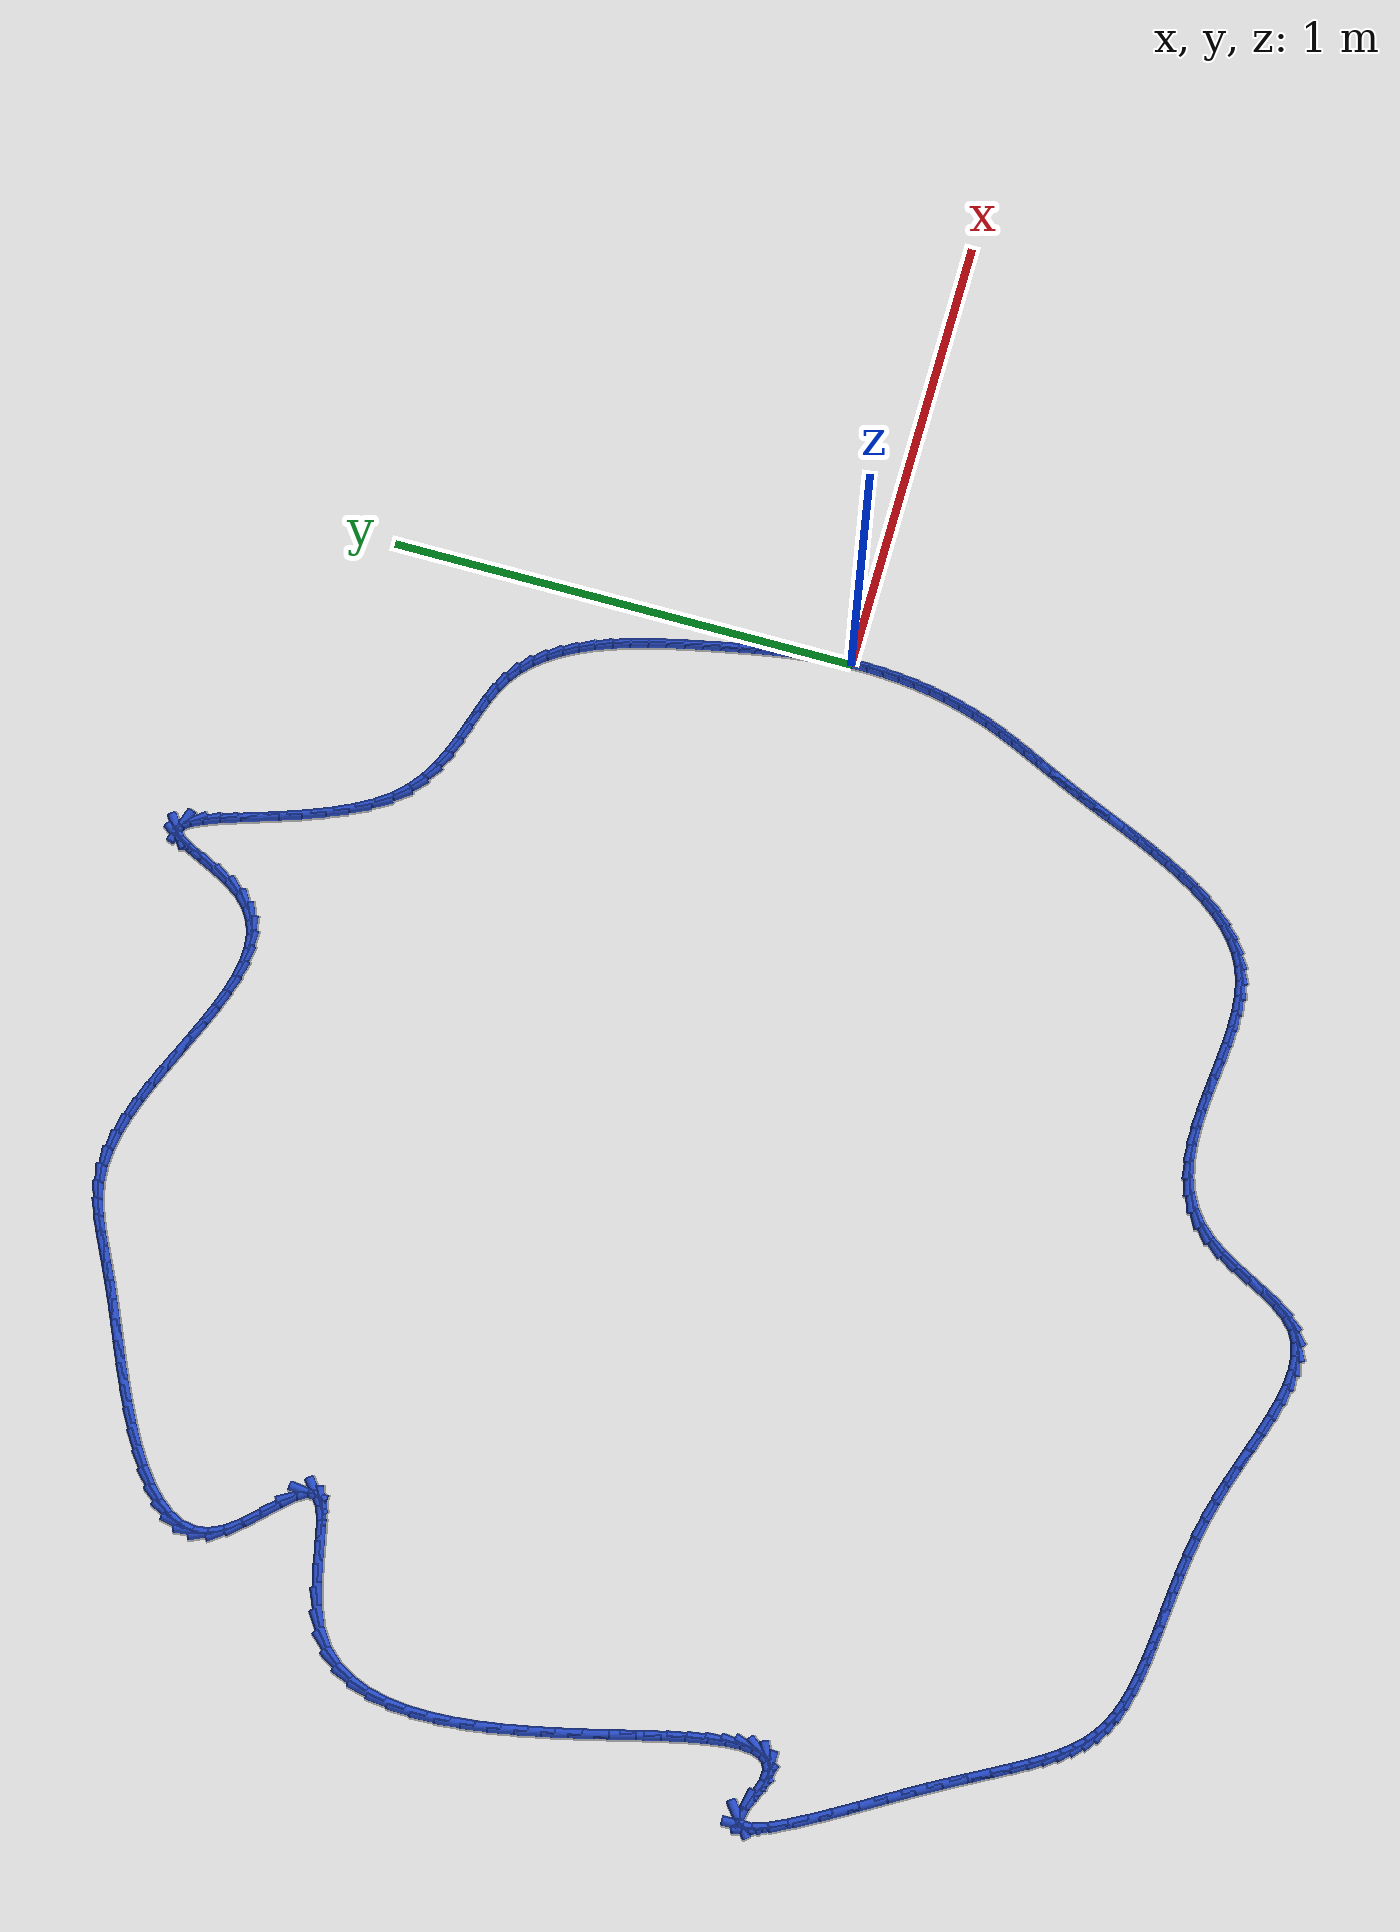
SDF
<sdf version="1.6">
 <world name="default">
  <light name="sun" type="directional">
   <pose>0 0 10 0 -0 0</pose>
   <diffuse>0.8 0.8 0.8 1</diffuse>
   <specular>0.2 0.2 0.2 1</specular>
   <attenuation>
    <range>1000</range>
    <constant>0.9</constant>
    <linear>0.01</linear>
    <quadratic>0.001</quadratic>
   </attenuation>
   <direction>-0.5 0.1 -0.9</direction>
  </light>
  <model name="ground_plane">
   <static>1</static>
   <link name="link">
    <collision name="collision">
     <geometry><plane><normal>0 0 1</normal><size>100 100</size></plane></geometry>
     <surface><friction><ode><mu>100</mu><mu2>50</mu2></ode></friction></surface>
    </collision>
    <visual name="visual">
     <cast_shadows>0</cast_shadows>
     <geometry><plane><normal>0 0 1</normal><size>100 100</size></plane></geometry>
     <material>
      <script><uri>file://media/materials/scripts/gazebo.material</uri><name>Gazebo/WhiteGlow</name></script>
     </material>
    </visual>
   </link>
  </model>
  <gravity>0 0 -9.8</gravity>
  <magnetic_field>6e-06 2.3e-05 -4.2e-05</magnetic_field>
  <atmosphere type="adiabatic"/>
  <physics name="default_physics" default="0" type="ode">
   <max_step_size>0.001</max_step_size>
   <real_time_factor>1</real_time_factor>
   <real_time_update_rate>1000</real_time_update_rate>
  </physics>
  <scene><ambient>0.4 0.4 0.4 1</ambient><background>0.7 0.7 0.7 1</background><shadows>1</shadows></scene>
  <spherical_coordinates>
   <surface_model>EARTH_WGS84</surface_model>
   <latitude_deg>0</latitude_deg>
   <longitude_deg>0</longitude_deg>
   <elevation>0</elevation>
   <heading_deg>0</heading_deg>
  </spherical_coordinates>
  <model name="line">
   <link name="link_0">
    <pose>-5.204170427930421e-18 2.7755575615628914e-17 0.01 0 1.57 -1.5295594090134041</pose>
    <collision name="collision">
     <geometry><cylinder><radius>0.01</radius><length>0.08</length></cylinder></geometry>
    </collision>
    <visual name="visual">
     <material>
      <script><name>Gazebo/Blue</name><uri>file://media/materials/scripts/gazebo.material</uri></script>
     </material>
     <geometry><cylinder><radius>0.01</radius><length>0.08</length></cylinder></geometry>
    </visual>
   </link>
   <link name="link_1">
    <pose>-0.0014169569345195586 0.03434188947827309 0.01 0 1.57 -1.492928567645868</pose>
    <collision name="collision">
     <geometry><cylinder><radius>0.01</radius><length>0.08</length></cylinder></geometry>
    </collision>
    <visual name="visual">
     <material>
      <script><name>Gazebo/Blue</name><uri>file://media/materials/scripts/gazebo.material</uri></script>
     </material>
     <geometry><cylinder><radius>0.01</radius><length>0.08</length></cylinder></geometry>
    </visual>
   </link>
   <link name="link_2">
    <pose>-0.004075083631085635 0.0684092895790169 0.01 0 1.57 -1.4604513469485967</pose>
    <collision name="collision">
     <geometry><cylinder><radius>0.01</radius><length>0.08</length></cylinder></geometry>
    </collision>
    <visual name="visual">
     <material>
      <script><name>Gazebo/Blue</name><uri>file://media/materials/scripts/gazebo.material</uri></script>
     </material>
     <geometry><cylinder><radius>0.01</radius><length>0.08</length></cylinder></geometry>
    </visual>
   </link>
   <link name="link_3">
    <pose>-0.007837845970132656 0.1023707631037121 0.01 0 1.57 -1.4326376824889024</pose>
    <collision name="collision">
     <geometry><cylinder><radius>0.01</radius><length>0.08</length></cylinder></geometry>
    </collision>
    <visual name="visual">
     <material>
      <script><name>Gazebo/Blue</name><uri>file://media/materials/scripts/gazebo.material</uri></script>
     </material>
     <geometry><cylinder><radius>0.01</radius><length>0.08</length></cylinder></geometry>
    </visual>
   </link>
   <link name="link_4">
    <pose>-0.012568709832095036 0.13639487285383922 0.01 0 1.57 -1.4098197949192002</pose>
    <collision name="collision">
     <geometry><cylinder><radius>0.01</radius><length>0.08</length></cylinder></geometry>
    </collision>
    <visual name="visual">
     <material>
      <script><name>Gazebo/Blue</name><uri>file://media/materials/scripts/gazebo.material</uri></script>
     </material>
     <geometry><cylinder><radius>0.01</radius><length>0.08</length></cylinder></geometry>
    </visual>
   </link>
   <link name="link_5">
    <pose>-0.018131141097407207 0.17065018163087892 0.01 0 1.57 -1.39215696415325</pose>
    <collision name="collision">
     <geometry><cylinder><radius>0.01</radius><length>0.08</length></cylinder></geometry>
    </collision>
    <visual name="visual">
     <material>
      <script><name>Gazebo/Blue</name><uri>file://media/materials/scripts/gazebo.material</uri></script>
     </material>
     <geometry><cylinder><radius>0.01</radius><length>0.08</length></cylinder></geometry>
    </visual>
   </link>
   <link name="link_6">
    <pose>-0.024388605646503577 0.20530525223631177 0.01 0 1.57 -1.3796520291454994</pose>
    <collision name="collision">
     <geometry><cylinder><radius>0.01</radius><length>0.08</length></cylinder></geometry>
    </collision>
    <visual name="visual">
     <material>
      <script><name>Gazebo/Blue</name><uri>file://media/materials/scripts/gazebo.material</uri></script>
     </material>
     <geometry><cylinder><radius>0.01</radius><length>0.08</length></cylinder></geometry>
    </visual>
   </link>
   <link name="link_7">
    <pose>-0.03120456935981857 0.24052864747161834 0.01 0 1.57 -1.372162680434083</pose>
    <collision name="collision">
     <geometry><cylinder><radius>0.01</radius><length>0.08</length></cylinder></geometry>
    </collision>
    <visual name="visual">
     <material>
      <script><name>Gazebo/Blue</name><uri>file://media/materials/scripts/gazebo.material</uri></script>
     </material>
     <geometry><cylinder><radius>0.01</radius><length>0.08</length></cylinder></geometry>
    </visual>
   </link>
   <link name="link_8">
    <pose>-0.03844282927552442 0.27648837904686263 0.01 0 1.57 -1.366423891915562</pose>
    <collision name="collision">
     <geometry><cylinder><radius>0.01</radius><length>0.08</length></cylinder></geometry>
    </collision>
    <visual name="visual">
     <material>
      <script><name>Gazebo/Blue</name><uri>file://media/materials/scripts/gazebo.material</uri></script>
     </material>
     <geometry><cylinder><radius>0.01</radius><length>0.08</length></cylinder></geometry>
    </visual>
   </link>
   <link name="link_9">
    <pose>-0.04605367447657129 0.3132085241719294 0.01 0 1.57 -1.3553191319393685</pose>
    <collision name="collision">
     <geometry><cylinder><radius>0.01</radius><length>0.08</length></cylinder></geometry>
    </collision>
    <visual name="visual">
     <material>
      <script><name>Gazebo/Blue</name><uri>file://media/materials/scripts/gazebo.material</uri></script>
     </material>
     <geometry><cylinder><radius>0.01</radius><length>0.08</length></cylinder></geometry>
    </visual>
   </link>
   <link name="link_10">
    <pose>-0.05418905659707783 0.3503775662043218 0.01 0 1.57 -1.3378294844939285</pose>
    <collision name="collision">
     <geometry><cylinder><radius>0.01</radius><length>0.08</length></cylinder></geometry>
    </collision>
    <visual name="visual">
     <material>
      <script><name>Gazebo/Blue</name><uri>file://media/materials/scripts/gazebo.material</uri></script>
     </material>
     <geometry><cylinder><radius>0.01</radius><length>0.08</length></cylinder></geometry>
    </visual>
   </link>
   <link name="link_11">
    <pose>-0.06302961277472323 0.38763625193076445 0.01 0 1.57 -1.3136647814946891</pose>
    <collision name="collision">
     <geometry><cylinder><radius>0.01</radius><length>0.08</length></cylinder></geometry>
    </collision>
    <visual name="visual">
     <material>
      <script><name>Gazebo/Blue</name><uri>file://media/materials/scripts/gazebo.material</uri></script>
     </material>
     <geometry><cylinder><radius>0.01</radius><length>0.08</length></cylinder></geometry>
    </visual>
   </link>
   <link name="link_12">
    <pose>-0.07275598014718661 0.4246253281379812 0.01 0 1.57 -1.2822499783672037</pose>
    <collision name="collision">
     <geometry><cylinder><radius>0.01</radius><length>0.08</length></cylinder></geometry>
    </collision>
    <visual name="visual">
     <material>
      <script><name>Gazebo/Blue</name><uri>file://media/materials/scripts/gazebo.material</uri></script>
     </material>
     <geometry><cylinder><radius>0.01</radius><length>0.08</length></cylinder></geometry>
    </visual>
   </link>
   <link name="link_13">
    <pose>-0.0835487958521471 0.46098554161269617 0.01 0 1.57 -1.2427185880478226</pose>
    <collision name="collision">
     <geometry><cylinder><radius>0.01</radius><length>0.08</length></cylinder></geometry>
    </collision>
    <visual name="visual">
     <material>
      <script><name>Gazebo/Blue</name><uri>file://media/materials/scripts/gazebo.material</uri></script>
     </material>
     <geometry><cylinder><radius>0.01</radius><length>0.08</length></cylinder></geometry>
    </visual>
   </link>
   <link name="link_14">
    <pose>-0.09558869702728386 0.4963576391416338 0.01 0 1.57 -1.1938997068330766</pose>
    <collision name="collision">
     <geometry><cylinder><radius>0.01</radius><length>0.08</length></cylinder></geometry>
    </collision>
    <visual name="visual">
     <material>
      <script><name>Gazebo/Blue</name><uri>file://media/materials/scripts/gazebo.material</uri></script>
     </material>
     <geometry><cylinder><radius>0.01</radius><length>0.08</length></cylinder></geometry>
    </visual>
   </link>
   <link name="link_15">
    <pose>-0.10905632081027611 0.5303823675115183 0.01 0 1.57 -1.1343165302581957</pose>
    <collision name="collision">
     <geometry><cylinder><radius>0.01</radius><length>0.08</length></cylinder></geometry>
    </collision>
    <visual name="visual">
     <material>
      <script><name>Gazebo/Blue</name><uri>file://media/materials/scripts/gazebo.material</uri></script>
     </material>
     <geometry><cylinder><radius>0.01</radius><length>0.08</length></cylinder></geometry>
    </visual>
   </link>
   <link name="link_16">
    <pose>-0.12413230433880296 0.5627004735090739 0.01 0 1.57 -1.062229290019738</pose>
    <collision name="collision">
     <geometry><cylinder><radius>0.01</radius><length>0.08</length></cylinder></geometry>
    </collision>
    <visual name="visual">
     <material>
      <script><name>Gazebo/Blue</name><uri>file://media/materials/scripts/gazebo.material</uri></script>
     </material>
     <geometry><cylinder><radius>0.01</radius><length>0.08</length></cylinder></geometry>
    </visual>
   </link>
   <link name="link_17">
    <pose>-0.14099728475054352 0.5929527039210245 0.01 0 1.57 -0.9757807442965027</pose>
    <collision name="collision">
     <geometry><cylinder><radius>0.01</radius><length>0.08</length></cylinder></geometry>
    </collision>
    <visual name="visual">
     <material>
      <script><name>Gazebo/Blue</name><uri>file://media/materials/scripts/gazebo.material</uri></script>
     </material>
     <geometry><cylinder><radius>0.01</radius><length>0.08</length></cylinder></geometry>
    </visual>
   </link>
   <link name="link_18">
    <pose>-0.15983189918317697 0.6207798055340946 0.01 0 1.57 -0.8733316935708395</pose>
    <collision name="collision">
     <geometry><cylinder><radius>0.01</radius><length>0.08</length></cylinder></geometry>
    </collision>
    <visual name="visual">
     <material>
      <script><name>Gazebo/Blue</name><uri>file://media/materials/scripts/gazebo.material</uri></script>
     </material>
     <geometry><cylinder><radius>0.01</radius><length>0.08</length></cylinder></geometry>
    </visual>
   </link>
   <link name="link_19">
    <pose>-0.1808167847743824 0.6458225251350083 0.01 0 1.57 -0.7540755938527375</pose>
    <collision name="collision">
     <geometry><cylinder><radius>0.01</radius><length>0.08</length></cylinder></geometry>
    </collision>
    <visual name="visual">
     <material>
      <script><name>Gazebo/Blue</name><uri>file://media/materials/scripts/gazebo.material</uri></script>
     </material>
     <geometry><cylinder><radius>0.01</radius><length>0.08</length></cylinder></geometry>
    </visual>
   </link>
   <link name="link_20">
    <pose>-0.20413257866183912 0.6677216095104896 0.01 0 1.57 -0.618920137825888</pose>
    <collision name="collision">
     <geometry><cylinder><radius>0.01</radius><length>0.08</length></cylinder></geometry>
    </collision>
    <visual name="visual">
     <material>
      <script><name>Gazebo/Blue</name><uri>file://media/materials/scripts/gazebo.material</uri></script>
     </material>
     <geometry><cylinder><radius>0.01</radius><length>0.08</length></cylinder></geometry>
    </visual>
   </link>
   <link name="link_21">
    <pose>-0.22995987966621645 0.6861178802591036 0.01 0 1.57 -0.4813224558688969</pose>
    <collision name="collision">
     <geometry><cylinder><radius>0.01</radius><length>0.08</length></cylinder></geometry>
    </collision>
    <visual name="visual">
     <material>
      <script><name>Gazebo/Blue</name><uri>file://media/materials/scripts/gazebo.material</uri></script>
     </material>
     <geometry><cylinder><radius>0.01</radius><length>0.08</length></cylinder></geometry>
    </visual>
   </link>
   <link name="link_22">
    <pose>-0.2583333297952614 0.700937131577133 0.01 0 1.57 -0.37784718666653777</pose>
    <collision name="collision">
     <geometry><cylinder><radius>0.01</radius><length>0.08</length></cylinder></geometry>
    </collision>
    <visual name="visual">
     <material>
      <script><name>Gazebo/Blue</name><uri>file://media/materials/scripts/gazebo.material</uri></script>
     </material>
     <geometry><cylinder><radius>0.01</radius><length>0.08</length></cylinder></geometry>
    </visual>
   </link>
   <link name="link_23">
    <pose>-0.28881157471532903 0.7130345141684127 0.01 0 1.57 -0.31437980762544593</pose>
    <collision name="collision">
     <geometry><cylinder><radius>0.01</radius><length>0.08</length></cylinder></geometry>
    </collision>
    <visual name="visual">
     <material>
      <script><name>Gazebo/Blue</name><uri>file://media/materials/scripts/gazebo.material</uri></script>
     </material>
     <geometry><cylinder><radius>0.01</radius><length>0.08</length></cylinder></geometry>
    </visual>
   </link>
   <link name="link_24">
    <pose>-0.32085638671139727 0.7234543186514414 0.01 0 1.57 -0.28769586318459905</pose>
    <collision name="collision">
     <geometry><cylinder><radius>0.01</radius><length>0.08</length></cylinder></geometry>
    </collision>
    <visual name="visual">
     <material>
      <script><name>Gazebo/Blue</name><uri>file://media/materials/scripts/gazebo.material</uri></script>
     </material>
     <geometry><cylinder><radius>0.01</radius><length>0.08</length></cylinder></geometry>
    </visual>
   </link>
   <link name="link_25">
    <pose>-0.35392953806844385 0.7332408356447183 0.01 0 1.57 -0.2949666757380576</pose>
    <collision name="collision">
     <geometry><cylinder><radius>0.01</radius><length>0.08</length></cylinder></geometry>
    </collision>
    <visual name="visual">
     <material>
      <script><name>Gazebo/Blue</name><uri>file://media/materials/scripts/gazebo.material</uri></script>
     </material>
     <geometry><cylinder><radius>0.01</radius><length>0.08</length></cylinder></geometry>
    </visual>
   </link>
   <link name="link_26">
    <pose>-0.38749280107144707 0.7434383557667423 0.01 0 1.57 -0.3346136339096233</pose>
    <collision name="collision">
     <geometry><cylinder><radius>0.01</radius><length>0.08</length></cylinder></geometry>
    </collision>
    <visual name="visual">
     <material>
      <script><name>Gazebo/Blue</name><uri>file://media/materials/scripts/gazebo.material</uri></script>
     </material>
     <geometry><cylinder><radius>0.01</radius><length>0.08</length></cylinder></geometry>
    </visual>
   </link>
   <link name="link_27">
    <pose>-0.4210079480053845 0.7550911696360121 0.01 0 1.57 -0.4059189672359612</pose>
    <collision name="collision">
     <geometry><cylinder><radius>0.01</radius><length>0.08</length></cylinder></geometry>
    </collision>
    <visual name="visual">
     <material>
      <script><name>Gazebo/Blue</name><uri>file://media/materials/scripts/gazebo.material</uri></script>
     </material>
     <geometry><cylinder><radius>0.01</radius><length>0.08</length></cylinder></geometry>
    </visual>
   </link>
   <link name="link_28">
    <pose>-0.4539367511552342 0.7692435678710267 0.01 0 1.57 -0.5077531292962789</pose>
    <collision name="collision">
     <geometry><cylinder><radius>0.01</radius><length>0.08</length></cylinder></geometry>
    </collision>
    <visual name="visual">
     <material>
      <script><name>Gazebo/Blue</name><uri>file://media/materials/scripts/gazebo.material</uri></script>
     </material>
     <geometry><cylinder><radius>0.01</radius><length>0.08</length></cylinder></geometry>
    </visual>
   </link>
   <link name="link_29">
    <pose>-0.48574098280597383 0.7869398410902848 0.01 0 1.57 -0.6366366953817574</pose>
    <collision name="collision">
     <geometry><cylinder><radius>0.01</radius><length>0.08</length></cylinder></geometry>
    </collision>
    <visual name="visual">
     <material>
      <script><name>Gazebo/Blue</name><uri>file://media/materials/scripts/gazebo.material</uri></script>
     </material>
     <geometry><cylinder><radius>0.01</radius><length>0.08</length></cylinder></geometry>
    </visual>
   </link>
   <link name="link_30">
    <pose>-0.5158824152425817 0.8092242799122857 0.01 0 1.57 -0.7849772611592256</pose>
    <collision name="collision">
     <geometry><cylinder><radius>0.01</radius><length>0.08</length></cylinder></geometry>
    </collision>
    <visual name="visual">
     <material>
      <script><name>Gazebo/Blue</name><uri>file://media/materials/scripts/gazebo.material</uri></script>
     </material>
     <geometry><cylinder><radius>0.01</radius><length>0.08</length></cylinder></geometry>
    </visual>
   </link>
   <link name="link_31">
    <pose>-0.543822820750036 0.8371411749555288 0.01 0 1.57 -0.9354698043360513</pose>
    <collision name="collision">
     <geometry><cylinder><radius>0.01</radius><length>0.08</length></cylinder></geometry>
    </collision>
    <visual name="visual">
     <material>
      <script><name>Gazebo/Blue</name><uri>file://media/materials/scripts/gazebo.material</uri></script>
     </material>
     <geometry><cylinder><radius>0.01</radius><length>0.08</length></cylinder></geometry>
    </visual>
   </link>
   <link name="link_32">
    <pose>-0.5691129564258318 0.8714419648784033 0.01 0 1.57 -1.050915930820242</pose>
    <collision name="collision">
     <geometry><cylinder><radius>0.01</radius><length>0.08</length></cylinder></geometry>
    </collision>
    <visual name="visual">
     <material>
      <script><name>Gazebo/Blue</name><uri>file://media/materials/scripts/gazebo.material</uri></script>
     </material>
     <geometry><cylinder><radius>0.01</radius><length>0.08</length></cylinder></geometry>
    </visual>
   </link>
   <link name="link_33">
    <pose>-0.5918332766480967 0.9111348370753205 0.01 0 1.57 -1.131353881538183</pose>
    <collision name="collision">
     <geometry><cylinder><radius>0.01</radius><length>0.08</length></cylinder></geometry>
    </collision>
    <visual name="visual">
     <material>
      <script><name>Gazebo/Blue</name><uri>file://media/materials/scripts/gazebo.material</uri></script>
     </material>
     <geometry><cylinder><radius>0.01</radius><length>0.08</length></cylinder></geometry>
    </visual>
   </link>
   <link name="link_34">
    <pose>-0.6122594403990578 0.9545855541345307 0.01 0 1.57 -1.1869152295459393</pose>
    <collision name="collision">
     <geometry><cylinder><radius>0.01</radius><length>0.08</length></cylinder></geometry>
    </collision>
    <visual name="visual">
     <material>
      <script><name>Gazebo/Blue</name><uri>file://media/materials/scripts/gazebo.material</uri></script>
     </material>
     <geometry><cylinder><radius>0.01</radius><length>0.08</length></cylinder></geometry>
    </visual>
   </link>
   <link name="link_35">
    <pose>-0.6306674132162439 1.0001588697606523 0.01 0 1.57 -1.2236290220097574</pose>
    <collision name="collision">
     <geometry><cylinder><radius>0.01</radius><length>0.08</length></cylinder></geometry>
    </collision>
    <visual name="visual">
     <material>
      <script><name>Gazebo/Blue</name><uri>file://media/materials/scripts/gazebo.material</uri></script>
     </material>
     <geometry><cylinder><radius>0.01</radius><length>0.08</length></cylinder></geometry>
    </visual>
   </link>
   <link name="link_36">
    <pose>-0.6473331606371838 1.0462195376583032 0.01 0 1.57 -1.2444726494711058</pose>
    <collision name="collision">
     <geometry><cylinder><radius>0.01</radius><length>0.08</length></cylinder></geometry>
    </collision>
    <visual name="visual">
     <material>
      <script><name>Gazebo/Blue</name><uri>file://media/materials/scripts/gazebo.material</uri></script>
     </material>
     <geometry><cylinder><radius>0.01</radius><length>0.08</length></cylinder></geometry>
    </visual>
   </link>
   <link name="link_37">
    <pose>-0.6625326481994066 1.0911323115321006 0.01 0 1.57 -1.2497726612800535</pose>
    <collision name="collision">
     <geometry><cylinder><radius>0.01</radius><length>0.08</length></cylinder></geometry>
    </collision>
    <visual name="visual">
     <material>
      <script><name>Gazebo/Blue</name><uri>file://media/materials/scripts/gazebo.material</uri></script>
     </material>
     <geometry><cylinder><radius>0.01</radius><length>0.08</length></cylinder></geometry>
    </visual>
   </link>
   <link name="link_38">
    <pose>-0.676541841440441 1.133261945086663 0.01 0 1.57 -1.236582155620675</pose>
    <collision name="collision">
     <geometry><cylinder><radius>0.01</radius><length>0.08</length></cylinder></geometry>
    </collision>
    <visual name="visual">
     <material>
      <script><name>Gazebo/Blue</name><uri>file://media/materials/scripts/gazebo.material</uri></script>
     </material>
     <geometry><cylinder><radius>0.01</radius><length>0.08</length></cylinder></geometry>
    </visual>
   </link>
   <link name="link_39">
    <pose>-0.689636705897816 1.1709731920266082 0.01 0 1.57 -1.195926985811713</pose>
    <collision name="collision">
     <geometry><cylinder><radius>0.01</radius><length>0.08</length></cylinder></geometry>
    </collision>
    <visual name="visual">
     <material>
      <script><name>Gazebo/Blue</name><uri>file://media/materials/scripts/gazebo.material</uri></script>
     </material>
     <geometry><cylinder><radius>0.01</radius><length>0.08</length></cylinder></geometry>
    </visual>
   </link>
   <link name="link_40">
    <pose>-0.7020932071090603 1.2026308060565538 0.01 0 1.57 -1.1034927882325485</pose>
    <collision name="collision">
     <geometry><cylinder><radius>0.01</radius><length>0.08</length></cylinder></geometry>
    </collision>
    <visual name="visual">
     <material>
      <script><name>Gazebo/Blue</name><uri>file://media/materials/scripts/gazebo.material</uri></script>
     </material>
     <geometry><cylinder><radius>0.01</radius><length>0.08</length></cylinder></geometry>
    </visual>
   </link>
   <link name="link_41">
    <pose>-0.7141873106117032 1.2265995408811186 0.01 0 1.57 -0.8840157648506225</pose>
    <collision name="collision">
     <geometry><cylinder><radius>0.01</radius><length>0.08</length></cylinder></geometry>
    </collision>
    <visual name="visual">
     <material>
      <script><name>Gazebo/Blue</name><uri>file://media/materials/scripts/gazebo.material</uri></script>
     </material>
     <geometry><cylinder><radius>0.01</radius><length>0.08</length></cylinder></geometry>
    </visual>
   </link>
   <link name="link_42">
    <pose>-0.7261949819432729 1.241244150204919 0.01 0 1.57 -0.2934169932314978</pose>
    <collision name="collision">
     <geometry><cylinder><radius>0.01</radius><length>0.08</length></cylinder></geometry>
    </collision>
    <visual name="visual">
     <material>
      <script><name>Gazebo/Blue</name><uri>file://media/materials/scripts/gazebo.material</uri></script>
     </material>
     <geometry><cylinder><radius>0.01</radius><length>0.08</length></cylinder></geometry>
    </visual>
   </link>
   <link name="link_43">
    <pose>-0.7383921866412987 1.2449293877325742 0.01 0 1.57 0.6130799242976773</pose>
    <collision name="collision">
     <geometry><cylinder><radius>0.01</radius><length>0.08</length></cylinder></geometry>
    </collision>
    <visual name="visual">
     <material>
      <script><name>Gazebo/Blue</name><uri>file://media/materials/scripts/gazebo.material</uri></script>
     </material>
     <geometry><cylinder><radius>0.01</radius><length>0.08</length></cylinder></geometry>
    </visual>
   </link>
   <link name="link_44">
    <pose>-0.7510549122303716 1.2360209931871597 0.01 0 1.57 1.0181445368010154</pose>
    <collision name="collision">
     <geometry><cylinder><radius>0.01</radius><length>0.08</length></cylinder></geometry>
    </collision>
    <visual name="visual">
     <material>
      <script><name>Gazebo/Blue</name><uri>file://media/materials/scripts/gazebo.material</uri></script>
     </material>
     <geometry><cylinder><radius>0.01</radius><length>0.08</length></cylinder></geometry>
    </visual>
   </link>
   <link name="link_45">
    <pose>-0.7644893392520428 1.2142387240140642 0.01 0 1.57 1.1293146660367903</pose>
    <collision name="collision">
     <geometry><cylinder><radius>0.01</radius><length>0.08</length></cylinder></geometry>
    </collision>
    <visual name="visual">
     <material>
      <script><name>Gazebo/Blue</name><uri>file://media/materials/scripts/gazebo.material</uri></script>
     </material>
     <geometry><cylinder><radius>0.01</radius><length>0.08</length></cylinder></geometry>
    </visual>
   </link>
   <link name="link_46">
    <pose>-0.7790916897498845 1.1833402842356449 0.01 0 1.57 1.1431556896960293</pose>
    <collision name="collision">
     <geometry><cylinder><radius>0.01</radius><length>0.08</length></cylinder></geometry>
    </collision>
    <visual name="visual">
     <material>
      <script><name>Gazebo/Blue</name><uri>file://media/materials/scripts/gazebo.material</uri></script>
     </material>
     <geometry><cylinder><radius>0.01</radius><length>0.08</length></cylinder></geometry>
    </visual>
   </link>
   <link name="link_47">
    <pose>-0.7952748963168429 1.1478327690341772 0.01 0 1.57 1.098820851667058</pose>
    <collision name="collision">
     <geometry><cylinder><radius>0.01</radius><length>0.08</length></cylinder></geometry>
    </collision>
    <visual name="visual">
     <material>
      <script><name>Gazebo/Blue</name><uri>file://media/materials/scripts/gazebo.material</uri></script>
     </material>
     <geometry><cylinder><radius>0.01</radius><length>0.08</length></cylinder></geometry>
    </visual>
   </link>
   <link name="link_48">
    <pose>-0.8134518915458646 1.1122232735919362 0.01 0 1.57 0.9877795945861113</pose>
    <collision name="collision">
     <geometry><cylinder><radius>0.01</radius><length>0.08</length></cylinder></geometry>
    </collision>
    <visual name="visual">
     <material>
      <script><name>Gazebo/Blue</name><uri>file://media/materials/scripts/gazebo.material</uri></script>
     </material>
     <geometry><cylinder><radius>0.01</radius><length>0.08</length></cylinder></geometry>
    </visual>
   </link>
   <link name="link_49">
    <pose>-0.8340348722163158 1.081012758287712 0.01 0 1.57 0.7967184467105943</pose>
    <collision name="collision">
     <geometry><cylinder><radius>0.01</radius><length>0.08</length></cylinder></geometry>
    </collision>
    <visual name="visual">
     <material>
      <script><name>Gazebo/Blue</name><uri>file://media/materials/scripts/gazebo.material</uri></script>
     </material>
     <geometry><cylinder><radius>0.01</radius><length>0.08</length></cylinder></geometry>
    </visual>
   </link>
   <link name="link_50">
    <pose>-0.8572622708435654 1.057253433922149 0.01 0 1.57 0.5722777304936463</pose>
    <collision name="collision">
     <geometry><cylinder><radius>0.01</radius><length>0.08</length></cylinder></geometry>
    </collision>
    <visual name="visual">
     <material>
      <script><name>Gazebo/Blue</name><uri>file://media/materials/scripts/gazebo.material</uri></script>
     </material>
     <geometry><cylinder><radius>0.01</radius><length>0.08</length></cylinder></geometry>
    </visual>
   </link>
   <link name="link_51">
    <pose>-0.8829757150570987 1.0406891733338695 0.01 0 1.57 0.34587273314613376</pose>
    <collision name="collision">
     <geometry><cylinder><radius>0.01</radius><length>0.08</length></cylinder></geometry>
    </collision>
    <visual name="visual">
     <material>
      <script><name>Gazebo/Blue</name><uri>file://media/materials/scripts/gazebo.material</uri></script>
     </material>
     <geometry><cylinder><radius>0.01</radius><length>0.08</length></cylinder></geometry>
    </visual>
   </link>
   <link name="link_52">
    <pose>-0.9109617006961301 1.030604191224311 0.01 0 1.57 0.14285401857127752</pose>
    <collision name="collision">
     <geometry><cylinder><radius>0.01</radius><length>0.08</length></cylinder></geometry>
    </collision>
    <visual name="visual">
     <material>
      <script><name>Gazebo/Blue</name><uri>file://media/materials/scripts/gazebo.material</uri></script>
     </material>
     <geometry><cylinder><radius>0.01</radius><length>0.08</length></cylinder></geometry>
    </visual>
   </link>
   <link name="link_53">
    <pose>-0.9410067235998725 1.0262827022949106 0.01 0 1.57 -0.022768290971229156</pose>
    <collision name="collision">
     <geometry><cylinder><radius>0.01</radius><length>0.08</length></cylinder></geometry>
    </collision>
    <visual name="visual">
     <material>
      <script><name>Gazebo/Blue</name><uri>file://media/materials/scripts/gazebo.material</uri></script>
     </material>
     <geometry><cylinder><radius>0.01</radius><length>0.08</length></cylinder></geometry>
    </visual>
   </link>
   <link name="link_54">
    <pose>-0.9728972796075404 1.027008921247107 0.01 0 1.57 -0.14975787793225118</pose>
    <collision name="collision">
     <geometry><cylinder><radius>0.01</radius><length>0.08</length></cylinder></geometry>
    </collision>
    <visual name="visual">
     <material>
      <script><name>Gazebo/Blue</name><uri>file://media/materials/scripts/gazebo.material</uri></script>
     </material>
     <geometry><cylinder><radius>0.01</radius><length>0.08</length></cylinder></geometry>
    </visual>
   </link>
   <link name="link_55">
    <pose>-1.0064198645583473 1.0320670627823374 0.01 0 1.57 -0.24333492597862233</pose>
    <collision name="collision">
     <geometry><cylinder><radius>0.01</radius><length>0.08</length></cylinder></geometry>
    </collision>
    <visual name="visual">
     <material>
      <script><name>Gazebo/Blue</name><uri>file://media/materials/scripts/gazebo.material</uri></script>
     </material>
     <geometry><cylinder><radius>0.01</radius><length>0.08</length></cylinder></geometry>
    </visual>
   </link>
   <link name="link_56">
    <pose>-1.041360974291507 1.0407413416020388 0.01 0 1.57 -0.3099004122861065</pose>
    <collision name="collision">
     <geometry><cylinder><radius>0.01</radius><length>0.08</length></cylinder></geometry>
    </collision>
    <visual name="visual">
     <material>
      <script><name>Gazebo/Blue</name><uri>file://media/materials/scripts/gazebo.material</uri></script>
     </material>
     <geometry><cylinder><radius>0.01</radius><length>0.08</length></cylinder></geometry>
    </visual>
   </link>
   <link name="link_57">
    <pose>-1.0775071046462337 1.0523159724076496 0.01 0 1.57 -0.35481252147726433</pose>
    <collision name="collision">
     <geometry><cylinder><radius>0.01</radius><length>0.08</length></cylinder></geometry>
    </collision>
    <visual name="visual">
     <material>
      <script><name>Gazebo/Blue</name><uri>file://media/materials/scripts/gazebo.material</uri></script>
     </material>
     <geometry><cylinder><radius>0.01</radius><length>0.08</length></cylinder></geometry>
    </visual>
   </link>
   <link name="link_58">
    <pose>-1.1146447514617401 1.0660751699006068 0.01 0 1.57 -0.38190877683297375</pose>
    <collision name="collision">
     <geometry><cylinder><radius>0.01</radius><length>0.08</length></cylinder></geometry>
    </collision>
    <visual name="visual">
     <material>
      <script><name>Gazebo/Blue</name><uri>file://media/materials/scripts/gazebo.material</uri></script>
     </material>
     <geometry><cylinder><radius>0.01</radius><length>0.08</length></cylinder></geometry>
    </visual>
   </link>
   <link name="link_59">
    <pose>-1.1525604105772411 1.0813031487823481 0.01 0 1.57 -0.39362963771132703</pose>
    <collision name="collision">
     <geometry><cylinder><radius>0.01</radius><length>0.08</length></cylinder></geometry>
    </collision>
    <visual name="visual">
     <material>
      <script><name>Gazebo/Blue</name><uri>file://media/materials/scripts/gazebo.material</uri></script>
     </material>
     <geometry><cylinder><radius>0.01</radius><length>0.08</length></cylinder></geometry>
    </visual>
   </link>
   <link name="link_60">
    <pose>-1.19104057783195 1.0972841237543112 0.01 0 1.57 -0.39124278950405356</pose>
    <collision name="collision">
     <geometry><cylinder><radius>0.01</radius><length>0.08</length></cylinder></geometry>
    </collision>
    <visual name="visual">
     <material>
      <script><name>Gazebo/Blue</name><uri>file://media/materials/scripts/gazebo.material</uri></script>
     </material>
     <geometry><cylinder><radius>0.01</radius><length>0.08</length></cylinder></geometry>
    </visual>
   </link>
   <link name="link_61">
    <pose>-1.229871749065081 1.113302309517934 0.01 0 1.57 -0.3750112583698487</pose>
    <collision name="collision">
     <geometry><cylinder><radius>0.01</radius><length>0.08</length></cylinder></geometry>
    </collision>
    <visual name="visual">
     <material>
      <script><name>Gazebo/Blue</name><uri>file://media/materials/scripts/gazebo.material</uri></script>
     </material>
     <geometry><cylinder><radius>0.01</radius><length>0.08</length></cylinder></geometry>
    </visual>
   </link>
   <link name="link_62">
    <pose>-1.268840420115847 1.1286419207746532 0.01 0 1.57 -0.34427785900492</pose>
    <collision name="collision">
     <geometry><cylinder><radius>0.01</radius><length>0.08</length></cylinder></geometry>
    </collision>
    <visual name="visual">
     <material>
      <script><name>Gazebo/Blue</name><uri>file://media/materials/scripts/gazebo.material</uri></script>
     </material>
     <geometry><cylinder><radius>0.01</radius><length>0.08</length></cylinder></geometry>
    </visual>
   </link>
   <link name="link_63">
    <pose>-1.307733086823463 1.1425871722259076 0.01 0 1.57 -0.2974860603792107</pose>
    <collision name="collision">
     <geometry><cylinder><radius>0.01</radius><length>0.08</length></cylinder></geometry>
    </collision>
    <visual name="visual">
     <material>
      <script><name>Gazebo/Blue</name><uri>file://media/materials/scripts/gazebo.material</uri></script>
     </material>
     <geometry><cylinder><radius>0.01</radius><length>0.08</length></cylinder></geometry>
    </visual>
   </link>
   <link name="link_64">
    <pose>-1.3463362450271412 1.1544222785731335 0.01 0 1.57 -0.23219548701608317</pose>
    <collision name="collision">
     <geometry><cylinder><radius>0.01</radius><length>0.08</length></cylinder></geometry>
    </collision>
    <visual name="visual">
     <material>
      <script><name>Gazebo/Blue</name><uri>file://media/materials/scripts/gazebo.material</uri></script>
     </material>
     <geometry><cylinder><radius>0.01</radius><length>0.08</length></cylinder></geometry>
    </visual>
   </link>
   <link name="link_65">
    <pose>-1.3844363905660964 1.163431454517769 0.01 0 1.57 -0.14522320170177352</pose>
    <collision name="collision">
     <geometry><cylinder><radius>0.01</radius><length>0.08</length></cylinder></geometry>
    </collision>
    <visual name="visual">
     <material>
      <script><name>Gazebo/Blue</name><uri>file://media/materials/scripts/gazebo.material</uri></script>
     </material>
     <geometry><cylinder><radius>0.01</radius><length>0.08</length></cylinder></geometry>
    </visual>
   </link>
   <link name="link_66">
    <pose>-1.4218200192795427 1.1688989147612523 0.01 0 1.57 -0.033179574759797645</pose>
    <collision name="collision">
     <geometry><cylinder><radius>0.01</radius><length>0.08</length></cylinder></geometry>
    </collision>
    <visual name="visual">
     <material>
      <script><name>Gazebo/Blue</name><uri>file://media/materials/scripts/gazebo.material</uri></script>
     </material>
     <geometry><cylinder><radius>0.01</radius><length>0.08</length></cylinder></geometry>
    </visual>
   </link>
   <link name="link_67">
    <pose>-1.458273627006693 1.1701088740050203 0.01 0 1.57 0.10603913842375869</pose>
    <collision name="collision">
     <geometry><cylinder><radius>0.01</radius><length>0.08</length></cylinder></geometry>
    </collision>
    <visual name="visual">
     <material>
      <script><name>Gazebo/Blue</name><uri>file://media/materials/scripts/gazebo.material</uri></script>
     </material>
     <geometry><cylinder><radius>0.01</radius><length>0.08</length></cylinder></geometry>
    </visual>
   </link>
   <link name="link_68">
    <pose>-1.493584416676293 1.1663504507755174 0.01 0 1.57 0.2526312601448719</pose>
    <collision name="collision">
     <geometry><cylinder><radius>0.01</radius><length>0.08</length></cylinder></geometry>
    </collision>
    <visual name="visual">
     <material>
      <script><name>Gazebo/Blue</name><uri>file://media/materials/scripts/gazebo.material</uri></script>
     </material>
     <geometry><cylinder><radius>0.01</radius><length>0.08</length></cylinder></geometry>
    </visual>
   </link>
   <link name="link_69">
    <pose>-1.5276330485499787 1.1575609112326115 0.01 0 1.57 0.366065053934845</pose>
    <collision name="collision">
     <geometry><cylinder><radius>0.01</radius><length>0.08</length></cylinder></geometry>
    </collision>
    <visual name="visual">
     <material>
      <script><name>Gazebo/Blue</name><uri>file://media/materials/scripts/gazebo.material</uri></script>
     </material>
     <geometry><cylinder><radius>0.01</radius><length>0.08</length></cylinder></geometry>
    </visual>
   </link>
   <link name="link_70">
    <pose>-1.560486102904276 1.144966918675247 0.01 0 1.57 0.44190268802495264</pose>
    <collision name="collision">
     <geometry><cylinder><radius>0.01</radius><length>0.08</length></cylinder></geometry>
    </collision>
    <visual name="visual">
     <material>
      <script><name>Gazebo/Blue</name><uri>file://media/materials/scripts/gazebo.material</uri></script>
     </material>
     <geometry><cylinder><radius>0.01</radius><length>0.08</length></cylinder></geometry>
    </visual>
   </link>
   <link name="link_71">
    <pose>-1.5922321499440586 1.1299476415036387 0.01 0 1.57 0.48174632583468585</pose>
    <collision name="collision">
     <geometry><cylinder><radius>0.01</radius><length>0.08</length></cylinder></geometry>
    </collision>
    <visual name="visual">
     <material>
      <script><name>Gazebo/Blue</name><uri>file://media/materials/scripts/gazebo.material</uri></script>
     </material>
     <geometry><cylinder><radius>0.01</radius><length>0.08</length></cylinder></geometry>
    </visual>
   </link>
   <link name="link_72">
    <pose>-1.6229597598741985 1.113882248118001 0.01 0 1.57 0.48869708060532124</pose>
    <collision name="collision">
     <geometry><cylinder><radius>0.01</radius><length>0.08</length></cylinder></geometry>
    </collision>
    <visual name="visual">
     <material>
      <script><name>Gazebo/Blue</name><uri>file://media/materials/scripts/gazebo.material</uri></script>
     </material>
     <geometry><cylinder><radius>0.01</radius><length>0.08</length></cylinder></geometry>
    </visual>
   </link>
   <link name="link_73">
    <pose>-1.6528910391575342 1.0979673168758388 0.01 0 1.57 0.4811240071334427</pose>
    <collision name="collision">
     <geometry><cylinder><radius>0.01</radius><length>0.08</length></cylinder></geometry>
    </collision>
    <visual name="visual">
     <material>
      <script><name>Gazebo/Blue</name><uri>file://media/materials/scripts/gazebo.material</uri></script>
     </material>
     <geometry><cylinder><radius>0.01</radius><length>0.08</length></cylinder></geometry>
    </visual>
   </link>
   <link name="link_74">
    <pose>-1.6831444299435103 1.0821738266323717 0.01 0 1.57 0.46798000543534257</pose>
    <collision name="collision">
     <geometry><cylinder><radius>0.01</radius><length>0.08</length></cylinder></geometry>
    </collision>
    <visual name="visual">
     <material>
      <script><name>Gazebo/Blue</name><uri>file://media/materials/scripts/gazebo.material</uri></script>
     </material>
     <geometry><cylinder><radius>0.01</radius><length>0.08</length></cylinder></geometry>
    </visual>
   </link>
   <link name="link_75">
    <pose>-1.7152072195528063 1.0659684178960958 0.01 0 1.57 0.4530268195718052</pose>
    <collision name="collision">
     <geometry><cylinder><radius>0.01</radius><length>0.08</length></cylinder></geometry>
    </collision>
    <visual name="visual">
     <material>
      <script><name>Gazebo/Blue</name><uri>file://media/materials/scripts/gazebo.material</uri></script>
     </material>
     <geometry><cylinder><radius>0.01</radius><length>0.08</length></cylinder></geometry>
    </visual>
   </link>
   <link name="link_76">
    <pose>-1.7503343571022705 1.0488687504789944 0.01 0 1.57 0.44626169773260055</pose>
    <collision name="collision">
     <geometry><cylinder><radius>0.01</radius><length>0.08</length></cylinder></geometry>
    </collision>
    <visual name="visual">
     <material>
      <script><name>Gazebo/Blue</name><uri>file://media/materials/scripts/gazebo.material</uri></script>
     </material>
     <geometry><cylinder><radius>0.01</radius><length>0.08</length></cylinder></geometry>
    </visual>
   </link>
   <link name="link_77">
    <pose>-1.7882132434256364 1.0307454931832851 0.01 0 1.57 0.4493194809005314</pose>
    <collision name="collision">
     <geometry><cylinder><radius>0.01</radius><length>0.08</length></cylinder></geometry>
    </collision>
    <visual name="visual">
     <material>
      <script><name>Gazebo/Blue</name><uri>file://media/materials/scripts/gazebo.material</uri></script>
     </material>
     <geometry><cylinder><radius>0.01</radius><length>0.08</length></cylinder></geometry>
    </visual>
   </link>
   <link name="link_78">
    <pose>-1.8278860915795807 1.0116146099119112 0.01 0 1.57 0.4610487964530609</pose>
    <collision name="collision">
     <geometry><cylinder><radius>0.01</radius><length>0.08</length></cylinder></geometry>
    </collision>
    <visual name="visual">
     <material>
      <script><name>Gazebo/Blue</name><uri>file://media/materials/scripts/gazebo.material</uri></script>
     </material>
     <geometry><cylinder><radius>0.01</radius><length>0.08</length></cylinder></geometry>
    </visual>
   </link>
   <link name="link_79">
    <pose>-1.8683931170451047 0.9914925144181854 0.01 0 1.57 0.481438530296922</pose>
    <collision name="collision">
     <geometry><cylinder><radius>0.01</radius><length>0.08</length></cylinder></geometry>
    </collision>
    <visual name="visual">
     <material>
      <script><name>Gazebo/Blue</name><uri>file://media/materials/scripts/gazebo.material</uri></script>
     </material>
     <geometry><cylinder><radius>0.01</radius><length>0.08</length></cylinder></geometry>
    </visual>
   </link>
   <link name="link_80">
    <pose>-1.9087745353032057 0.970395620455421 0.01 0 1.57 0.5114468252621107</pose>
    <collision name="collision">
     <geometry><cylinder><radius>0.01</radius><length>0.08</length></cylinder></geometry>
    </collision>
    <visual name="visual">
     <material>
      <script><name>Gazebo/Blue</name><uri>file://media/materials/scripts/gazebo.material</uri></script>
     </material>
     <geometry><cylinder><radius>0.01</radius><length>0.08</length></cylinder></geometry>
    </visual>
   </link>
   <link name="link_81">
    <pose>-1.9480705618348846 0.9483403417769302 0.01 0 1.57 0.5530877667774309</pose>
    <collision name="collision">
     <geometry><cylinder><radius>0.01</radius><length>0.08</length></cylinder></geometry>
    </collision>
    <visual name="visual">
     <material>
      <script><name>Gazebo/Blue</name><uri>file://media/materials/scripts/gazebo.material</uri></script>
     </material>
     <geometry><cylinder><radius>0.01</radius><length>0.08</length></cylinder></geometry>
    </visual>
   </link>
   <link name="link_82">
    <pose>-1.9853214121211393 0.9253430921360262 0.01 0 1.57 0.6097588334511302</pose>
    <collision name="collision">
     <geometry><cylinder><radius>0.01</radius><length>0.08</length></cylinder></geometry>
    </collision>
    <visual name="visual">
     <material>
      <script><name>Gazebo/Blue</name><uri>file://media/materials/scripts/gazebo.material</uri></script>
     </material>
     <geometry><cylinder><radius>0.01</radius><length>0.08</length></cylinder></geometry>
    </visual>
   </link>
   <link name="link_83">
    <pose>-2.019567301642969 0.9014202852860208 0.01 0 1.57 0.6868455316124791</pose>
    <collision name="collision">
     <geometry><cylinder><radius>0.01</radius><length>0.08</length></cylinder></geometry>
    </collision>
    <visual name="visual">
     <material>
      <script><name>Gazebo/Blue</name><uri>file://media/materials/scripts/gazebo.material</uri></script>
     </material>
     <geometry><cylinder><radius>0.01</radius><length>0.08</length></cylinder></geometry>
    </visual>
   </link>
   <link name="link_84">
    <pose>-2.049848445881374 0.8765883349802277 0.01 0 1.57 0.7926035250982975</pose>
    <collision name="collision">
     <geometry><cylinder><radius>0.01</radius><length>0.08</length></cylinder></geometry>
    </collision>
    <visual name="visual">
     <material>
      <script><name>Gazebo/Blue</name><uri>file://media/materials/scripts/gazebo.material</uri></script>
     </material>
     <geometry><cylinder><radius>0.01</radius><length>0.08</length></cylinder></geometry>
    </visual>
   </link>
   <link name="link_85">
    <pose>-2.075205060317353 0.8508636549719591 0.01 0 1.57 0.9389060124912676</pose>
    <collision name="collision">
     <geometry><cylinder><radius>0.01</radius><length>0.08</length></cylinder></geometry>
    </collision>
    <visual name="visual">
     <material>
      <script><name>Gazebo/Blue</name><uri>file://media/materials/scripts/gazebo.material</uri></script>
     </material>
     <geometry><cylinder><radius>0.01</radius><length>0.08</length></cylinder></geometry>
    </visual>
   </link>
   <link name="link_86">
    <pose>-2.094677360431904 0.8242626590145278 0.01 0 1.57 1.139772160502898</pose>
    <collision name="collision">
     <geometry><cylinder><radius>0.01</radius><length>0.08</length></cylinder></geometry>
    </collision>
    <visual name="visual">
     <material>
      <script><name>Gazebo/Blue</name><uri>file://media/materials/scripts/gazebo.material</uri></script>
     </material>
     <geometry><cylinder><radius>0.01</radius><length>0.08</length></cylinder></geometry>
    </visual>
   </link>
   <link name="link_87">
    <pose>-2.1073055617060272 0.7968017608612468 0.01 0 1.57 1.4019744992765353</pose>
    <collision name="collision">
     <geometry><cylinder><radius>0.01</radius><length>0.08</length></cylinder></geometry>
    </collision>
    <visual name="visual">
     <material>
      <script><name>Gazebo/Blue</name><uri>file://media/materials/scripts/gazebo.material</uri></script>
     </material>
     <geometry><cylinder><radius>0.01</radius><length>0.08</length></cylinder></geometry>
    </visual>
   </link>
   <link name="link_88">
    <pose>-2.112129879620723 0.768497374265428 0.01 0 1.57 -1.4363850107947265</pose>
    <collision name="collision">
     <geometry><cylinder><radius>0.01</radius><length>0.08</length></cylinder></geometry>
    </collision>
    <visual name="visual">
     <material>
      <script><name>Gazebo/Blue</name><uri>file://media/materials/scripts/gazebo.material</uri></script>
     </material>
     <geometry><cylinder><radius>0.01</radius><length>0.08</length></cylinder></geometry>
    </visual>
   </link>
   <link name="link_89">
    <pose>-2.108190529656988 0.7393659129803849 0.01 0 1.57 -1.1427244110443526</pose>
    <collision name="collision">
     <geometry><cylinder><radius>0.01</radius><length>0.08</length></cylinder></geometry>
    </collision>
    <visual name="visual">
     <material>
      <script><name>Gazebo/Blue</name><uri>file://media/materials/scripts/gazebo.material</uri></script>
     </material>
     <geometry><cylinder><radius>0.01</radius><length>0.08</length></cylinder></geometry>
    </visual>
   </link>
   <link name="link_90">
    <pose>-2.094528302604822 0.709423895216642 0.01 0 1.57 -0.9233310152574232</pose>
    <collision name="collision">
     <geometry><cylinder><radius>0.01</radius><length>0.08</length></cylinder></geometry>
    </collision>
    <visual name="visual">
     <material>
      <script><name>Gazebo/Blue</name><uri>file://media/materials/scripts/gazebo.material</uri></script>
     </material>
     <geometry><cylinder><radius>0.01</radius><length>0.08</length></cylinder></geometry>
    </visual>
   </link>
   <link name="link_91">
    <pose>-2.071460592598484 0.6789196284087013 0.01 0 1.57 -0.8184438780672131</pose>
    <collision name="collision">
     <geometry><cylinder><radius>0.01</radius><length>0.08</length></cylinder></geometry>
    </collision>
    <visual name="visual">
     <material>
      <script><name>Gazebo/Blue</name><uri>file://media/materials/scripts/gazebo.material</uri></script>
     </material>
     <geometry><cylinder><radius>0.01</radius><length>0.08</length></cylinder></geometry>
    </visual>
   </link>
   <link name="link_92">
    <pose>-2.043292429935153 0.6488254437027827 0.01 0 1.57 -0.7921575952335149</pose>
    <collision name="collision">
     <geometry><cylinder><radius>0.01</radius><length>0.08</length></cylinder></geometry>
    </collision>
    <visual name="visual">
     <material>
      <script><name>Gazebo/Blue</name><uri>file://media/materials/scripts/gazebo.material</uri></script>
     </material>
     <geometry><cylinder><radius>0.01</radius><length>0.08</length></cylinder></geometry>
    </visual>
   </link>
   <link name="link_93">
    <pose>-2.015105293179226 0.6202546497398991 0.01 0 1.57 -0.8426030125410588</pose>
    <collision name="collision">
     <geometry><cylinder><radius>0.01</radius><length>0.08</length></cylinder></geometry>
    </collision>
    <visual name="visual">
     <material>
      <script><name>Gazebo/Blue</name><uri>file://media/materials/scripts/gazebo.material</uri></script>
     </material>
     <geometry><cylinder><radius>0.01</radius><length>0.08</length></cylinder></geometry>
    </visual>
   </link>
   <link name="link_94">
    <pose>-1.9919806608951023 0.5943205551610621 0.01 0 1.57 -1.04137990059905</pose>
    <collision name="collision">
     <geometry><cylinder><radius>0.01</radius><length>0.08</length></cylinder></geometry>
    </collision>
    <visual name="visual">
     <material>
      <script><name>Gazebo/Blue</name><uri>file://media/materials/scripts/gazebo.material</uri></script>
     </material>
     <geometry><cylinder><radius>0.01</radius><length>0.08</length></cylinder></geometry>
    </visual>
   </link>
   <link name="link_95">
    <pose>-1.9790000116471802 0.5721364686072847 0.01 0 1.57 1.4696708230710651</pose>
    <collision name="collision">
     <geometry><cylinder><radius>0.01</radius><length>0.08</length></cylinder></geometry>
    </collision>
    <visual name="visual">
     <material>
      <script><name>Gazebo/Blue</name><uri>file://media/materials/scripts/gazebo.material</uri></script>
     </material>
     <geometry><cylinder><radius>0.01</radius><length>0.08</length></cylinder></geometry>
    </visual>
   </link>
   <link name="link_96">
    <pose>-1.9807724440730832 0.5546691988354628 0.01 0 1.57 0.6835913863024506</pose>
    <collision name="collision">
     <geometry><cylinder><radius>0.01</radius><length>0.08</length></cylinder></geometry>
    </collision>
    <visual name="visual">
     <material>
      <script><name>Gazebo/Blue</name><uri>file://media/materials/scripts/gazebo.material</uri></script>
     </material>
     <geometry><cylinder><radius>0.01</radius><length>0.08</length></cylinder></geometry>
    </visual>
   </link>
   <link name="link_97">
    <pose>-1.9970766462465654 0.5413874922426668 0.01 0 1.57 0.36144930947251863</pose>
    <collision name="collision">
     <geometry><cylinder><radius>0.01</radius><length>0.08</length></cylinder></geometry>
    </collision>
    <visual name="visual">
     <material>
      <script><name>Gazebo/Blue</name><uri>file://media/materials/scripts/gazebo.material</uri></script>
     </material>
     <geometry><cylinder><radius>0.01</radius><length>0.08</length></cylinder></geometry>
    </visual>
   </link>
   <link name="link_98">
    <pose>-2.024862533997269 0.5308828039134791 0.01 0 1.57 0.24762685957653766</pose>
    <collision name="collision">
     <geometry><cylinder><radius>0.01</radius><length>0.08</length></cylinder></geometry>
    </collision>
    <visual name="visual">
     <material>
      <script><name>Gazebo/Blue</name><uri>file://media/materials/scripts/gazebo.material</uri></script>
     </material>
     <geometry><cylinder><radius>0.01</radius><length>0.08</length></cylinder></geometry>
    </visual>
   </link>
   <link name="link_99">
    <pose>-2.061044263977869 0.5217354988861347 0.01 0 1.57 0.21842025667227843</pose>
    <collision name="collision">
     <geometry><cylinder><radius>0.01</radius><length>0.08</length></cylinder></geometry>
    </collision>
    <visual name="visual">
     <material>
      <script><name>Gazebo/Blue</name><uri>file://media/materials/scripts/gazebo.material</uri></script>
     </material>
     <geometry><cylinder><radius>0.01</radius><length>0.08</length></cylinder></geometry>
    </visual>
   </link>
   <link name="link_100">
    <pose>-2.10253599284104 0.5125259421988688 0.01 0 1.57 0.23985833245882765</pose>
    <collision name="collision">
     <geometry><cylinder><radius>0.01</radius><length>0.08</length></cylinder></geometry>
    </collision>
    <visual name="visual">
     <material>
      <script><name>Gazebo/Blue</name><uri>file://media/materials/scripts/gazebo.material</uri></script>
     </material>
     <geometry><cylinder><radius>0.01</radius><length>0.08</length></cylinder></geometry>
    </visual>
   </link>
   <link name="link_101">
    <pose>-2.146251877239458 0.5018344988899163 0.01 0 1.57 0.3071527815555674</pose>
    <collision name="collision">
     <geometry><cylinder><radius>0.01</radius><length>0.08</length></cylinder></geometry>
    </collision>
    <visual name="visual">
     <material>
      <script><name>Gazebo/Blue</name><uri>file://media/materials/scripts/gazebo.material</uri></script>
     </material>
     <geometry><cylinder><radius>0.01</radius><length>0.08</length></cylinder></geometry>
    </visual>
   </link>
   <link name="link_102">
    <pose>-2.189106073825796 0.48824153399751247 0.01 0 1.57 0.4315004876409992</pose>
    <collision name="collision">
     <geometry><cylinder><radius>0.01</radius><length>0.08</length></cylinder></geometry>
    </collision>
    <visual name="visual">
     <material>
      <script><name>Gazebo/Blue</name><uri>file://media/materials/scripts/gazebo.material</uri></script>
     </material>
     <geometry><cylinder><radius>0.01</radius><length>0.08</length></cylinder></geometry>
    </visual>
   </link>
   <link name="link_103">
    <pose>-2.22801273925273 0.47032741255989163 0.01 0 1.57 0.6258583096492476</pose>
    <collision name="collision">
     <geometry><cylinder><radius>0.01</radius><length>0.08</length></cylinder></geometry>
    </collision>
    <visual name="visual">
     <material>
      <script><name>Gazebo/Blue</name><uri>file://media/materials/scripts/gazebo.material</uri></script>
     </material>
     <geometry><cylinder><radius>0.01</radius><length>0.08</length></cylinder></geometry>
    </visual>
   </link>
   <link name="link_104">
    <pose>-2.2603738118354477 0.4469371417761886 0.01 0 1.57 0.842280792043314</pose>
    <collision name="collision">
     <geometry><cylinder><radius>0.01</radius><length>0.08</length></cylinder></geometry>
    </collision>
    <visual name="visual">
     <material>
      <script><name>Gazebo/Blue</name><uri>file://media/materials/scripts/gazebo.material</uri></script>
     </material>
     <geometry><cylinder><radius>0.01</radius><length>0.08</length></cylinder></geometry>
    </visual>
   </link>
   <link name="link_105">
    <pose>-2.2859961639725257 0.41822050719527565 0.01 0 1.57 1.0450971705151095</pose>
    <collision name="collision">
     <geometry><cylinder><radius>0.01</radius><length>0.08</length></cylinder></geometry>
    </collision>
    <visual name="visual">
     <material>
      <script><name>Gazebo/Blue</name><uri>file://media/materials/scripts/gazebo.material</uri></script>
     </material>
     <geometry><cylinder><radius>0.01</radius><length>0.08</length></cylinder></geometry>
    </visual>
   </link>
   <link name="link_106">
    <pose>-2.305426564627525 0.3847287195134809 0.01 0 1.57 1.2203718458545298</pose>
    <collision name="collision">
     <geometry><cylinder><radius>0.01</radius><length>0.08</length></cylinder></geometry>
    </collision>
    <visual name="visual">
     <material>
      <script><name>Gazebo/Blue</name><uri>file://media/materials/scripts/gazebo.material</uri></script>
     </material>
     <geometry><cylinder><radius>0.01</radius><length>0.08</length></cylinder></geometry>
    </visual>
   </link>
   <link name="link_107">
    <pose>-2.3192119861203406 0.3470130997565326 0.01 0 1.57 1.3638988463719883</pose>
    <collision name="collision">
     <geometry><cylinder><radius>0.01</radius><length>0.08</length></cylinder></geometry>
    </collision>
    <visual name="visual">
     <material>
      <script><name>Gazebo/Blue</name><uri>file://media/materials/scripts/gazebo.material</uri></script>
     </material>
     <geometry><cylinder><radius>0.01</radius><length>0.08</length></cylinder></geometry>
    </visual>
   </link>
   <link name="link_108">
    <pose>-2.3278994007708653 0.3056249689501594 0.01 0 1.57 1.4781295909732357</pose>
    <collision name="collision">
     <geometry><cylinder><radius>0.01</radius><length>0.08</length></cylinder></geometry>
    </collision>
    <visual name="visual">
     <material>
      <script><name>Gazebo/Blue</name><uri>file://media/materials/scripts/gazebo.material</uri></script>
     </material>
     <geometry><cylinder><radius>0.01</radius><length>0.08</length></cylinder></geometry>
    </visual>
   </link>
   <link name="link_109">
    <pose>-2.332035780898994 0.2611156481200916 0.01 0 1.57 1.5679857946316658</pose>
    <collision name="collision">
     <geometry><cylinder><radius>0.01</radius><length>0.08</length></cylinder></geometry>
    </collision>
    <visual name="visual">
     <material>
      <script><name>Gazebo/Blue</name><uri>file://media/materials/scripts/gazebo.material</uri></script>
     </material>
     <geometry><cylinder><radius>0.01</radius><length>0.08</length></cylinder></geometry>
    </visual>
   </link>
   <link name="link_110">
    <pose>-2.332168098824622 0.21403645829205672 0.01 0 1.57 -1.5031821359105366</pose>
    <collision name="collision">
     <geometry><cylinder><radius>0.01</radius><length>0.08</length></cylinder></geometry>
    </collision>
    <visual name="visual">
     <material>
      <script><name>Gazebo/Blue</name><uri>file://media/materials/scripts/gazebo.material</uri></script>
     </material>
     <geometry><cylinder><radius>0.01</radius><length>0.08</length></cylinder></geometry>
    </visual>
   </link>
   <link name="link_111">
    <pose>-2.3288433268676414 0.16493872049178546 0.01 0 1.57 -1.448111058988455</pose>
    <collision name="collision">
     <geometry><cylinder><radius>0.01</radius><length>0.08</length></cylinder></geometry>
    </collision>
    <visual name="visual">
     <material>
      <script><name>Gazebo/Blue</name><uri>file://media/materials/scripts/gazebo.material</uri></script>
     </material>
     <geometry><cylinder><radius>0.01</radius><length>0.08</length></cylinder></geometry>
    </visual>
   </link>
   <link name="link_112">
    <pose>-2.3226084373479465 0.11437375574500522 0.01 0 1.57 -1.4053095594165699</pose>
    <collision name="collision">
     <geometry><cylinder><radius>0.01</radius><length>0.08</length></cylinder></geometry>
    </collision>
    <visual name="visual">
     <material>
      <script><name>Gazebo/Blue</name><uri>file://media/materials/scripts/gazebo.material</uri></script>
     </material>
     <geometry><cylinder><radius>0.01</radius><length>0.08</length></cylinder></geometry>
    </visual>
   </link>
   <link name="link_113">
    <pose>-2.314010402585433 0.06289288507744663 0.01 0 1.57 -1.3725641641813793</pose>
    <collision name="collision">
     <geometry><cylinder><radius>0.01</radius><length>0.08</length></cylinder></geometry>
    </collision>
    <visual name="visual">
     <material>
      <script><name>Gazebo/Blue</name><uri>file://media/materials/scripts/gazebo.material</uri></script>
     </material>
     <geometry><cylinder><radius>0.01</radius><length>0.08</length></cylinder></geometry>
    </visual>
   </link>
   <link name="link_114">
    <pose>-2.3035961948999937 0.01104742951483733 0.01 0 1.57 -1.3483730397441898</pose>
    <collision name="collision">
     <geometry><cylinder><radius>0.01</radius><length>0.08</length></cylinder></geometry>
    </collision>
    <visual name="visual">
     <material>
      <script><name>Gazebo/Blue</name><uri>file://media/materials/scripts/gazebo.material</uri></script>
     </material>
     <geometry><cylinder><radius>0.01</radius><length>0.08</length></cylinder></geometry>
    </visual>
   </link>
   <link name="link_115">
    <pose>-2.2919127866115234 -0.04061128991709231 0.01 0 1.57 -1.3318249322705378</pose>
    <collision name="collision">
     <geometry><cylinder><radius>0.01</radius><length>0.08</length></cylinder></geometry>
    </collision>
    <visual name="visual">
     <material>
      <script><name>Gazebo/Blue</name><uri>file://media/materials/scripts/gazebo.material</uri></script>
     </material>
     <geometry><cylinder><radius>0.01</radius><length>0.08</length></cylinder></geometry>
    </visual>
   </link>
   <link name="link_116">
    <pose>-2.2795071500399158 -0.09153195219261394 0.01 0 1.57 -1.3225383467863738</pose>
    <collision name="collision">
     <geometry><cylinder><radius>0.01</radius><length>0.08</length></cylinder></geometry>
    </collision>
    <visual name="visual">
     <material>
      <script><name>Gazebo/Blue</name><uri>file://media/materials/scripts/gazebo.material</uri></script>
     </material>
     <geometry><cylinder><radius>0.01</radius><length>0.08</length></cylinder></geometry>
    </visual>
   </link>
   <link name="link_117">
    <pose>-2.266926257505065 -0.1411632362859998 0.01 0 1.57 -1.320673823356376</pose>
    <collision name="collision">
     <geometry><cylinder><radius>0.01</radius><length>0.08</length></cylinder></geometry>
    </collision>
    <visual name="visual">
     <material>
      <script><name>Gazebo/Blue</name><uri>file://media/materials/scripts/gazebo.material</uri></script>
     </material>
     <geometry><cylinder><radius>0.01</radius><length>0.08</length></cylinder></geometry>
    </visual>
   </link>
   <link name="link_118">
    <pose>-2.254717081326865 -0.18895382117151804 0.01 0 1.57 -1.327044378228869</pose>
    <collision name="collision">
     <geometry><cylinder><radius>0.01</radius><length>0.08</length></cylinder></geometry>
    </collision>
    <visual name="visual">
     <material>
      <script><name>Gazebo/Blue</name><uri>file://media/materials/scripts/gazebo.material</uri></script>
     </material>
     <geometry><cylinder><radius>0.01</radius><length>0.08</length></cylinder></geometry>
    </visual>
   </link>
   <link name="link_119">
    <pose>-2.2434265938252103 -0.23435238582344117 0.01 0 1.57 -1.3433833077350472</pose>
    <collision name="collision">
     <geometry><cylinder><radius>0.01</radius><length>0.08</length></cylinder></geometry>
    </collision>
    <visual name="visual">
     <material>
      <script><name>Gazebo/Blue</name><uri>file://media/materials/scripts/gazebo.material</uri></script>
     </material>
     <geometry><cylinder><radius>0.01</radius><length>0.08</length></cylinder></geometry>
    </visual>
   </link>
   <link name="link_120">
    <pose>-2.233601767319995 -0.2768076092160401 0.01 0 1.57 -1.3729052220481435</pose>
    <collision name="collision">
     <geometry><cylinder><radius>0.01</radius><length>0.08</length></cylinder></geometry>
    </collision>
    <visual name="visual">
     <material>
      <script><name>Gazebo/Blue</name><uri>file://media/materials/scripts/gazebo.material</uri></script>
     </material>
     <geometry><cylinder><radius>0.01</radius><length>0.08</length></cylinder></geometry>
    </visual>
   </link>
   <link name="link_121">
    <pose>-2.2257895741311122 -0.3157681703235857 0.01 0 1.57 -1.4214750117214412</pose>
    <collision name="collision">
     <geometry><cylinder><radius>0.01</radius><length>0.08</length></cylinder></geometry>
    </collision>
    <visual name="visual">
     <material>
      <script><name>Gazebo/Blue</name><uri>file://media/materials/scripts/gazebo.material</uri></script>
     </material>
     <geometry><cylinder><radius>0.01</radius><length>0.08</length></cylinder></geometry>
    </visual>
   </link>
   <link name="link_122">
    <pose>-2.220536986578457 -0.35068274812034983 0.01 0 1.57 -1.5001291500045086</pose>
    <collision name="collision">
     <geometry><cylinder><radius>0.01</radius><length>0.08</length></cylinder></geometry>
    </collision>
    <visual name="visual">
     <material>
      <script><name>Gazebo/Blue</name><uri>file://media/materials/scripts/gazebo.material</uri></script>
     </material>
     <geometry><cylinder><radius>0.01</radius><length>0.08</length></cylinder></geometry>
    </visual>
   </link>
   <link name="link_123">
    <pose>-2.2183909769819246 -0.38100002158060164 0.01 0 1.57 1.510970242069487</pose>
    <collision name="collision">
     <geometry><cylinder><radius>0.01</radius><length>0.08</length></cylinder></geometry>
    </collision>
    <visual name="visual">
     <material>
      <script><name>Gazebo/Blue</name><uri>file://media/materials/scripts/gazebo.material</uri></script>
     </material>
     <geometry><cylinder><radius>0.01</radius><length>0.08</length></cylinder></geometry>
    </visual>
   </link>
   <link name="link_124">
    <pose>-2.219898517661407 -0.406168669678613 0.01 0 1.57 1.2855972516038467</pose>
    <collision name="collision">
     <geometry><cylinder><radius>0.01</radius><length>0.08</length></cylinder></geometry>
    </collision>
    <visual name="visual">
     <material>
      <script><name>Gazebo/Blue</name><uri>file://media/materials/scripts/gazebo.material</uri></script>
     </material>
     <geometry><cylinder><radius>0.01</radius><length>0.08</length></cylinder></geometry>
    </visual>
   </link>
   <link name="link_125">
    <pose>-2.2256065809367986 -0.4256373713886549 0.01 0 1.57 0.9015409147351732</pose>
    <collision name="collision">
     <geometry><cylinder><radius>0.01</radius><length>0.08</length></cylinder></geometry>
    </collision>
    <visual name="visual">
     <material>
      <script><name>Gazebo/Blue</name><uri>file://media/materials/scripts/gazebo.material</uri></script>
     </material>
     <geometry><cylinder><radius>0.01</radius><length>0.08</length></cylinder></geometry>
    </visual>
   </link>
   <link name="link_126">
    <pose>-2.236062139127995 -0.43885480568499846 0.01 0 1.57 0.3867759997725727</pose>
    <collision name="collision">
     <geometry><cylinder><radius>0.01</radius><length>0.08</length></cylinder></geometry>
    </collision>
    <visual name="visual">
     <material>
      <script><name>Gazebo/Blue</name><uri>file://media/materials/scripts/gazebo.material</uri></script>
     </material>
     <geometry><cylinder><radius>0.01</radius><length>0.08</length></cylinder></geometry>
    </visual>
   </link>
   <link name="link_127">
    <pose>-2.251812164554889 -0.445269651541914 0.01 0 1.57 -0.04346496052852654</pose>
    <collision name="collision">
     <geometry><cylinder><radius>0.01</radius><length>0.08</length></cylinder></geometry>
    </collision>
    <visual name="visual">
     <material>
      <script><name>Gazebo/Blue</name><uri>file://media/materials/scripts/gazebo.material</uri></script>
     </material>
     <geometry><cylinder><radius>0.01</radius><length>0.08</length></cylinder></geometry>
    </visual>
   </link>
   <link name="link_128">
    <pose>-2.2734036295373743 -0.4443305879336731 0.01 0 1.57 -0.3061565032385815</pose>
    <collision name="collision">
     <geometry><cylinder><radius>0.01</radius><length>0.08</length></cylinder></geometry>
    </collision>
    <visual name="visual">
     <material>
      <script><name>Gazebo/Blue</name><uri>file://media/materials/scripts/gazebo.material</uri></script>
     </material>
     <geometry><cylinder><radius>0.01</radius><length>0.08</length></cylinder></geometry>
    </visual>
   </link>
   <link name="link_129">
    <pose>-2.3013835063953465 -0.4354862938345463 0.01 0 1.57 -0.4165431866689635</pose>
    <collision name="collision">
     <geometry><cylinder><radius>0.01</radius><length>0.08</length></cylinder></geometry>
    </collision>
    <visual name="visual">
     <material>
      <script><name>Gazebo/Blue</name><uri>file://media/materials/scripts/gazebo.material</uri></script>
     </material>
     <geometry><cylinder><radius>0.01</radius><length>0.08</length></cylinder></geometry>
    </visual>
   </link>
   <link name="link_130">
    <pose>-2.3334718456817205 -0.4212893624390932 0.01 0 1.57 -0.19980132769813047</pose>
    <collision name="collision">
     <geometry><cylinder><radius>0.01</radius><length>0.08</length></cylinder></geometry>
    </collision>
    <visual name="visual">
     <material>
      <script><name>Gazebo/Blue</name><uri>file://media/materials/scripts/gazebo.material</uri></script>
     </material>
     <geometry><cylinder><radius>0.01</radius><length>0.08</length></cylinder></geometry>
    </visual>
   </link>
   <link name="link_131">
    <pose>-2.3560819848695234 -0.4167107367243325 0.01 0 1.57 0.690418639364166</pose>
    <collision name="collision">
     <geometry><cylinder><radius>0.01</radius><length>0.08</length></cylinder></geometry>
    </collision>
    <visual name="visual">
     <material>
      <script><name>Gazebo/Blue</name><uri>file://media/materials/scripts/gazebo.material</uri></script>
     </material>
     <geometry><cylinder><radius>0.01</radius><length>0.08</length></cylinder></geometry>
    </visual>
   </link>
   <link name="link_132">
    <pose>-2.3662326235308346 -0.42509557187338476 0.01 0 1.57 -1.5407085488992551</pose>
    <collision name="collision">
     <geometry><cylinder><radius>0.01</radius><length>0.08</length></cylinder></geometry>
    </collision>
    <visual name="visual">
     <material>
      <script><name>Gazebo/Blue</name><uri>file://media/materials/scripts/gazebo.material</uri></script>
     </material>
     <geometry><cylinder><radius>0.01</radius><length>0.08</length></cylinder></geometry>
    </visual>
   </link>
   <link name="link_133">
    <pose>-2.3656446407254066 -0.44463192208735464 0.01 0 1.57 -1.2496852060123054</pose>
    <collision name="collision">
     <geometry><cylinder><radius>0.01</radius><length>0.08</length></cylinder></geometry>
    </collision>
    <visual name="visual">
     <material>
      <script><name>Gazebo/Blue</name><uri>file://media/materials/scripts/gazebo.material</uri></script>
     </material>
     <geometry><cylinder><radius>0.01</radius><length>0.08</length></cylinder></geometry>
    </visual>
   </link>
   <link name="link_134">
    <pose>-2.3560403798864846 -0.47350623551949866 0.01 0 1.57 -1.1361535164169765</pose>
    <collision name="collision">
     <geometry><cylinder><radius>0.01</radius><length>0.08</length></cylinder></geometry>
    </collision>
    <visual name="visual">
     <material>
      <script><name>Gazebo/Blue</name><uri>file://media/materials/scripts/gazebo.material</uri></script>
     </material>
     <geometry><cylinder><radius>0.01</radius><length>0.08</length></cylinder></geometry>
    </visual>
   </link>
   <link name="link_135">
    <pose>-2.3391421844473177 -0.509904960323074 0.01 0 1.57 -1.0806293332593608</pose>
    <collision name="collision">
     <geometry><cylinder><radius>0.01</radius><length>0.08</length></cylinder></geometry>
    </collision>
    <visual name="visual">
     <material>
      <script><name>Gazebo/Blue</name><uri>file://media/materials/scripts/gazebo.material</uri></script>
     </material>
     <geometry><cylinder><radius>0.01</radius><length>0.08</length></cylinder></geometry>
    </visual>
   </link>
   <link name="link_136">
    <pose>-2.316672397841152 -0.5520145446513346 0.01 0 1.57 -1.0511689099415722</pose>
    <collision name="collision">
     <geometry><cylinder><radius>0.01</radius><length>0.08</length></cylinder></geometry>
    </collision>
    <visual name="visual">
     <material>
      <script><name>Gazebo/Blue</name><uri>file://media/materials/scripts/gazebo.material</uri></script>
     </material>
     <geometry><cylinder><radius>0.01</radius><length>0.08</length></cylinder></geometry>
    </visual>
   </link>
   <link name="link_137">
    <pose>-2.290353363501236 -0.5980214366575378 0.01 0 1.57 -1.036645333680963</pose>
    <collision name="collision">
     <geometry><cylinder><radius>0.01</radius><length>0.08</length></cylinder></geometry>
    </collision>
    <visual name="visual">
     <material>
      <script><name>Gazebo/Blue</name><uri>file://media/materials/scripts/gazebo.material</uri></script>
     </material>
     <geometry><cylinder><radius>0.01</radius><length>0.08</length></cylinder></geometry>
    </visual>
   </link>
   <link name="link_138">
    <pose>-2.261907424860816 -0.6461120844949397 0.01 0 1.57 -1.0329047436988237</pose>
    <collision name="collision">
     <geometry><cylinder><radius>0.01</radius><length>0.08</length></cylinder></geometry>
    </collision>
    <visual name="visual">
     <material>
      <script><name>Gazebo/Blue</name><uri>file://media/materials/scripts/gazebo.material</uri></script>
     </material>
     <geometry><cylinder><radius>0.01</radius><length>0.08</length></cylinder></geometry>
    </visual>
   </link>
   <link name="link_139">
    <pose>-2.2330569253531407 -0.6944729363167967 0.01 0 1.57 -1.0391831996601</pose>
    <collision name="collision">
     <geometry><cylinder><radius>0.01</radius><length>0.08</length></cylinder></geometry>
    </collision>
    <visual name="visual">
     <material>
      <script><name>Gazebo/Blue</name><uri>file://media/materials/scripts/gazebo.material</uri></script>
     </material>
     <geometry><cylinder><radius>0.01</radius><length>0.08</length></cylinder></geometry>
    </visual>
   </link>
   <link name="link_140">
    <pose>-2.205524207258031 -0.7412904412593584 0.01 0 1.57 -1.0541353261785522</pose>
    <collision name="collision">
     <geometry><cylinder><radius>0.01</radius><length>0.08</length></cylinder></geometry>
    </collision>
    <visual name="visual">
     <material>
      <script><name>Gazebo/Blue</name><uri>file://media/materials/scripts/gazebo.material</uri></script>
     </material>
     <geometry><cylinder><radius>0.01</radius><length>0.08</length></cylinder></geometry>
    </visual>
   </link>
   <link name="link_141">
    <pose>-2.1806458718883723 -0.7850797918117443 0.01 0 1.57 -1.066630038948523</pose>
    <collision name="collision">
     <geometry><cylinder><radius>0.01</radius><length>0.08</length></cylinder></geometry>
    </collision>
    <visual name="visual">
     <material>
      <script><name>Gazebo/Blue</name><uri>file://media/materials/scripts/gazebo.material</uri></script>
     </material>
     <geometry><cylinder><radius>0.01</radius><length>0.08</length></cylinder></geometry>
    </visual>
   </link>
   <link name="link_142">
    <pose>-2.158281739668689 -0.8256147501829274 0.01 0 1.57 -1.072115189011889</pose>
    <collision name="collision">
     <geometry><cylinder><radius>0.01</radius><length>0.08</length></cylinder></geometry>
    </collision>
    <visual name="visual">
     <material>
      <script><name>Gazebo/Blue</name><uri>file://media/materials/scripts/gazebo.material</uri></script>
     </material>
     <geometry><cylinder><radius>0.01</radius><length>0.08</length></cylinder></geometry>
    </visual>
   </link>
   <link name="link_143">
    <pose>-2.137938277713015 -0.8629702199228185 0.01 0 1.57 -1.0684388120397101</pose>
    <collision name="collision">
     <geometry><cylinder><radius>0.01</radius><length>0.08</length></cylinder></geometry>
    </collision>
    <visual name="visual">
     <material>
      <script><name>Gazebo/Blue</name><uri>file://media/materials/scripts/gazebo.material</uri></script>
     </material>
     <geometry><cylinder><radius>0.01</radius><length>0.08</length></cylinder></geometry>
    </visual>
   </link>
   <link name="link_144">
    <pose>-2.119121953135384 -0.8972211045813286 0.01 0 1.57 -1.0530509741519318</pose>
    <collision name="collision">
     <geometry><cylinder><radius>0.01</radius><length>0.08</length></cylinder></geometry>
    </collision>
    <visual name="visual">
     <material>
      <script><name>Gazebo/Blue</name><uri>file://media/materials/scripts/gazebo.material</uri></script>
     </material>
     <geometry><cylinder><radius>0.01</radius><length>0.08</length></cylinder></geometry>
    </visual>
   </link>
   <link name="link_145">
    <pose>-2.1013392330498344 -0.9284423077083669 0.01 0 1.57 -1.0230529833752908</pose>
    <collision name="collision">
     <geometry><cylinder><radius>0.01</radius><length>0.08</length></cylinder></geometry>
    </collision>
    <visual name="visual">
     <material>
      <script><name>Gazebo/Blue</name><uri>file://media/materials/scripts/gazebo.material</uri></script>
     </material>
     <geometry><cylinder><radius>0.01</radius><length>0.08</length></cylinder></geometry>
    </visual>
   </link>
   <link name="link_146">
    <pose>-2.084096584570397 -0.9567087328538445 0.01 0 1.57 -0.9754196909352094</pose>
    <collision name="collision">
     <geometry><cylinder><radius>0.01</radius><length>0.08</length></cylinder></geometry>
    </collision>
    <visual name="visual">
     <material>
      <script><name>Gazebo/Blue</name><uri>file://media/materials/scripts/gazebo.material</uri></script>
     </material>
     <geometry><cylinder><radius>0.01</radius><length>0.08</length></cylinder></geometry>
    </visual>
   </link>
   <link name="link_147">
    <pose>-2.066900474811108 -0.9820952835676717 0.01 0 1.57 -0.9075591068767468</pose>
    <collision name="collision">
     <geometry><cylinder><radius>0.01</radius><length>0.08</length></cylinder></geometry>
    </collision>
    <visual name="visual">
     <material>
      <script><name>Gazebo/Blue</name><uri>file://media/materials/scripts/gazebo.material</uri></script>
     </material>
     <geometry><cylinder><radius>0.01</radius><length>0.08</length></cylinder></geometry>
    </visual>
   </link>
   <link name="link_148">
    <pose>-2.0492573708860022 -1.0046768633997598 0.01 0 1.57 -0.8183737637136564</pose>
    <collision name="collision">
     <geometry><cylinder><radius>0.01</radius><length>0.08</length></cylinder></geometry>
    </collision>
    <visual name="visual">
     <material>
      <script><name>Gazebo/Blue</name><uri>file://media/materials/scripts/gazebo.material</uri></script>
     </material>
     <geometry><cylinder><radius>0.01</radius><length>0.08</length></cylinder></geometry>
    </visual>
   </link>
   <link name="link_149">
    <pose>-2.030673739909115 -1.0245283759000183 0.01 0 1.57 -0.7097289984119729</pose>
    <collision name="collision">
     <geometry><cylinder><radius>0.01</radius><length>0.08</length></cylinder></geometry>
    </collision>
    <visual name="visual">
     <material>
      <script><name>Gazebo/Blue</name><uri>file://media/materials/scripts/gazebo.material</uri></script>
     </material>
     <geometry><cylinder><radius>0.01</radius><length>0.08</length></cylinder></geometry>
    </visual>
   </link>
   <link name="link_150">
    <pose>-2.0106560489944796 -1.0417247246183576 0.01 0 1.57 -0.5875582443266087</pose>
    <collision name="collision">
     <geometry><cylinder><radius>0.01</radius><length>0.08</length></cylinder></geometry>
    </collision>
    <visual name="visual">
     <material>
      <script><name>Gazebo/Blue</name><uri>file://media/materials/scripts/gazebo.material</uri></script>
     </material>
     <geometry><cylinder><radius>0.01</radius><length>0.08</length></cylinder></geometry>
    </visual>
   </link>
   <link name="link_151">
    <pose>-1.9887107832509143 -1.0563408203340143 0.01 0 1.57 -0.465094078132118</pose>
    <collision name="collision">
     <geometry><cylinder><radius>0.01</radius><length>0.08</length></cylinder></geometry>
    </collision>
    <visual name="visual">
     <material>
      <script><name>Gazebo/Blue</name><uri>file://media/materials/scripts/gazebo.material</uri></script>
     </material>
     <geometry><cylinder><radius>0.01</radius><length>0.08</length></cylinder></geometry>
    </visual>
   </link>
   <link name="link_152">
    <pose>-1.9644733769165337 -1.0685033785744023 0.01 0 1.57 -0.36177064715580853</pose>
    <collision name="collision">
     <geometry><cylinder><radius>0.01</radius><length>0.08</length></cylinder></geometry>
    </collision>
    <visual name="visual">
     <material>
      <script><name>Gazebo/Blue</name><uri>file://media/materials/scripts/gazebo.material</uri></script>
     </material>
     <geometry><cylinder><radius>0.01</radius><length>0.08</length></cylinder></geometry>
    </visual>
   </link>
   <link name="link_153">
    <pose>-1.9380172288868491 -1.078515065250714 0.01 0 1.57 -0.28009820476621494</pose>
    <collision name="collision">
     <geometry><cylinder><radius>0.01</radius><length>0.08</length></cylinder></geometry>
    </collision>
    <visual name="visual">
     <material>
      <script><name>Gazebo/Blue</name><uri>file://media/materials/scripts/gazebo.material</uri></script>
     </material>
     <geometry><cylinder><radius>0.01</radius><length>0.08</length></cylinder></geometry>
    </visual>
   </link>
   <link name="link_154">
    <pose>-1.9095086332498676 -1.086715866511047 0.01 0 1.57 -0.21790110370147547</pose>
    <collision name="collision">
     <geometry><cylinder><radius>0.01</radius><length>0.08</length></cylinder></geometry>
    </collision>
    <visual name="visual">
     <material>
      <script><name>Gazebo/Blue</name><uri>file://media/materials/scripts/gazebo.material</uri></script>
     </material>
     <geometry><cylinder><radius>0.01</radius><length>0.08</length></cylinder></geometry>
    </visual>
   </link>
   <link name="link_155">
    <pose>-1.879113884093596 -1.093445768503501 0.01 0 1.57 -0.1726090751510088</pose>
    <collision name="collision">
     <geometry><cylinder><radius>0.01</radius><length>0.08</length></cylinder></geometry>
    </collision>
    <visual name="visual">
     <material>
      <script><name>Gazebo/Blue</name><uri>file://media/materials/scripts/gazebo.material</uri></script>
     </material>
     <geometry><cylinder><radius>0.01</radius><length>0.08</length></cylinder></geometry>
    </visual>
   </link>
   <link name="link_156">
    <pose>-1.846999275506039 -1.0990447573761721 0.01 0 1.57 -0.14184823405291397</pose>
    <collision name="collision">
     <geometry><cylinder><radius>0.01</radius><length>0.08</length></cylinder></geometry>
    </collision>
    <visual name="visual">
     <material>
      <script><name>Gazebo/Blue</name><uri>file://media/materials/scripts/gazebo.material</uri></script>
     </material>
     <geometry><cylinder><radius>0.01</radius><length>0.08</length></cylinder></geometry>
    </visual>
   </link>
   <link name="link_157">
    <pose>-1.8133311015752032 -1.1038528192771604 0.01 0 1.57 -0.12365809827191325</pose>
    <collision name="collision">
     <geometry><cylinder><radius>0.01</radius><length>0.08</length></cylinder></geometry>
    </collision>
    <visual name="visual">
     <material>
      <script><name>Gazebo/Blue</name><uri>file://media/materials/scripts/gazebo.material</uri></script>
     </material>
     <geometry><cylinder><radius>0.01</radius><length>0.08</length></cylinder></geometry>
    </visual>
   </link>
   <link name="link_158">
    <pose>-1.7782756563890958 -1.108209940354563 0.01 0 1.57 -0.11652009960904468</pose>
    <collision name="collision">
     <geometry><cylinder><radius>0.01</radius><length>0.08</length></cylinder></geometry>
    </collision>
    <visual name="visual">
     <material>
      <script><name>Gazebo/Blue</name><uri>file://media/materials/scripts/gazebo.material</uri></script>
     </material>
     <geometry><cylinder><radius>0.01</radius><length>0.08</length></cylinder></geometry>
    </visual>
   </link>
   <link name="link_159">
    <pose>-1.7419992340357222 -1.112456106756478 0.01 0 1.57 -0.11930917419888622</pose>
    <collision name="collision">
     <geometry><cylinder><radius>0.01</radius><length>0.08</length></cylinder></geometry>
    </collision>
    <visual name="visual">
     <material>
      <script><name>Gazebo/Blue</name><uri>file://media/materials/scripts/gazebo.material</uri></script>
     </material>
     <geometry><cylinder><radius>0.01</radius><length>0.08</length></cylinder></geometry>
    </visual>
   </link>
   <link name="link_160">
    <pose>-1.7046681286030885 -1.116931304631004 0.01 0 1.57 -0.1312217732455574</pose>
    <collision name="collision">
     <geometry><cylinder><radius>0.01</radius><length>0.08</length></cylinder></geometry>
    </collision>
    <visual name="visual">
     <material>
      <script><name>Gazebo/Blue</name><uri>file://media/materials/scripts/gazebo.material</uri></script>
     </material>
     <geometry><cylinder><radius>0.01</radius><length>0.08</length></cylinder></geometry>
    </visual>
   </link>
   <link name="link_161">
    <pose>-1.6664486341792009 -1.1219755201262387 0.01 0 1.57 -0.15170108787693526</pose>
    <collision name="collision">
     <geometry><cylinder><radius>0.01</radius><length>0.08</length></cylinder></geometry>
    </collision>
    <visual name="visual">
     <material>
      <script><name>Gazebo/Blue</name><uri>file://media/materials/scripts/gazebo.material</uri></script>
     </material>
     <geometry><cylinder><radius>0.01</radius><length>0.08</length></cylinder></geometry>
    </visual>
   </link>
   <link name="link_162">
    <pose>-1.6275070448520643 -1.1279287393902806 0.01 0 1.57 -0.18036482326261932</pose>
    <collision name="collision">
     <geometry><cylinder><radius>0.01</radius><length>0.08</length></cylinder></geometry>
    </collision>
    <visual name="visual">
     <material>
      <script><name>Gazebo/Blue</name><uri>file://media/materials/scripts/gazebo.material</uri></script>
     </material>
     <geometry><cylinder><radius>0.01</radius><length>0.08</length></cylinder></geometry>
    </visual>
   </link>
   <link name="link_163">
    <pose>-1.5880096547096876 -1.1351309485712278 0.01 0 1.57 -0.21693451267381825</pose>
    <collision name="collision">
     <geometry><cylinder><radius>0.01</radius><length>0.08</length></cylinder></geometry>
    </collision>
    <visual name="visual">
     <material>
      <script><name>Gazebo/Blue</name><uri>file://media/materials/scripts/gazebo.material</uri></script>
     </material>
     <geometry><cylinder><radius>0.01</radius><length>0.08</length></cylinder></geometry>
    </visual>
   </link>
   <link name="link_164">
    <pose>-1.5481227578400751 -1.1439221338171786 0.01 0 1.57 -0.26099706478267204</pose>
    <collision name="collision">
     <geometry><cylinder><radius>0.01</radius><length>0.08</length></cylinder></geometry>
    </collision>
    <visual name="visual">
     <material>
      <script><name>Gazebo/Blue</name><uri>file://media/materials/scripts/gazebo.material</uri></script>
     </material>
     <geometry><cylinder><radius>0.01</radius><length>0.08</length></cylinder></geometry>
    </visual>
   </link>
   <link name="link_165">
    <pose>-1.5080134126292237 -1.1546349167637222 0.01 0 1.57 -0.30296954171576435</pose>
    <collision name="collision">
     <geometry><cylinder><radius>0.01</radius><length>0.08</length></cylinder></geometry>
    </collision>
    <visual name="visual">
     <material>
      <script><name>Gazebo/Blue</name><uri>file://media/materials/scripts/gazebo.material</uri></script>
     </material>
     <geometry><cylinder><radius>0.01</radius><length>0.08</length></cylinder></geometry>
    </visual>
   </link>
   <link name="link_166">
    <pose>-1.4678928463636862 -1.167176322714948 0.01 0 1.57 -0.32945890005482553</pose>
    <collision name="collision">
     <geometry><cylinder><radius>0.01</radius><length>0.08</length></cylinder></geometry>
    </collision>
    <visual name="visual">
     <material>
      <script><name>Gazebo/Blue</name><uri>file://media/materials/scripts/gazebo.material</uri></script>
     </material>
     <geometry><cylinder><radius>0.01</radius><length>0.08</length></cylinder></geometry>
    </visual>
   </link>
   <link name="link_167">
    <pose>-1.4280397942293501 -1.1808028940799677 0.01 0 1.57 -0.3402517675445505</pose>
    <collision name="collision">
     <geometry><cylinder><radius>0.01</radius><length>0.08</length></cylinder></geometry>
    </collision>
    <visual name="visual">
     <material>
      <script><name>Gazebo/Blue</name><uri>file://media/materials/scripts/gazebo.material</uri></script>
     </material>
     <geometry><cylinder><radius>0.01</radius><length>0.08</length></cylinder></geometry>
    </visual>
   </link>
   <link name="link_168">
    <pose>-1.3887386884679884 -1.1947162783971745 0.01 0 1.57 -0.335265732886131</pose>
    <collision name="collision">
     <geometry><cylinder><radius>0.01</radius><length>0.08</length></cylinder></geometry>
    </collision>
    <visual name="visual">
     <material>
      <script><name>Gazebo/Blue</name><uri>file://media/materials/scripts/gazebo.material</uri></script>
     </material>
     <geometry><cylinder><radius>0.01</radius><length>0.08</length></cylinder></geometry>
    </visual>
   </link>
   <link name="link_169">
    <pose>-1.3502739613213735 -1.2081181232049614 0.01 0 1.57 -0.313145981653459</pose>
    <collision name="collision">
     <geometry><cylinder><radius>0.01</radius><length>0.08</length></cylinder></geometry>
    </collision>
    <visual name="visual">
     <material>
      <script><name>Gazebo/Blue</name><uri>file://media/materials/scripts/gazebo.material</uri></script>
     </material>
     <geometry><cylinder><radius>0.01</radius><length>0.08</length></cylinder></geometry>
    </visual>
   </link>
   <link name="link_170">
    <pose>-1.3129300450312786 -1.2202100760417214 0.01 0 1.57 -0.27096605962898695</pose>
    <collision name="collision">
     <geometry><cylinder><radius>0.01</radius><length>0.08</length></cylinder></geometry>
    </collision>
    <visual name="visual">
     <material>
      <script><name>Gazebo/Blue</name><uri>file://media/materials/scripts/gazebo.material</uri></script>
     </material>
     <geometry><cylinder><radius>0.01</radius><length>0.08</length></cylinder></geometry>
    </visual>
   </link>
   <link name="link_171">
    <pose>-1.2769913718394788 -1.2301937844458473 0.01 0 1.57 -0.20376910694771191</pose>
    <collision name="collision">
     <geometry><cylinder><radius>0.01</radius><length>0.08</length></cylinder></geometry>
    </collision>
    <visual name="visual">
     <material>
      <script><name>Gazebo/Blue</name><uri>file://media/materials/scripts/gazebo.material</uri></script>
     </material>
     <geometry><cylinder><radius>0.01</radius><length>0.08</length></cylinder></geometry>
    </visual>
   </link>
   <link name="link_172">
    <pose>-1.2427423739877457 -1.2372708959557317 0.01 0 1.57 -0.1041048019341289</pose>
    <collision name="collision">
     <geometry><cylinder><radius>0.01</radius><length>0.08</length></cylinder></geometry>
    </collision>
    <visual name="visual">
     <material>
      <script><name>Gazebo/Blue</name><uri>file://media/materials/scripts/gazebo.material</uri></script>
     </material>
     <geometry><cylinder><radius>0.01</radius><length>0.08</length></cylinder></geometry>
    </visual>
   </link>
   <link name="link_173">
    <pose>-1.2104674837178535 -1.2406430581097687 0.01 0 1.57 0.03766629391386478</pose>
    <collision name="collision">
     <geometry><cylinder><radius>0.01</radius><length>0.08</length></cylinder></geometry>
    </collision>
    <visual name="visual">
     <material>
      <script><name>Gazebo/Blue</name><uri>file://media/materials/scripts/gazebo.material</uri></script>
     </material>
     <geometry><cylinder><radius>0.01</radius><length>0.08</length></cylinder></geometry>
    </visual>
   </link>
   <link name="link_174">
    <pose>-1.1804511332715748 -1.23951191844635 0.01 0 1.57 0.2300029245848729</pose>
    <collision name="collision">
     <geometry><cylinder><radius>0.01</radius><length>0.08</length></cylinder></geometry>
    </collision>
    <visual name="visual">
     <material>
      <script><name>Gazebo/Blue</name><uri>file://media/materials/scripts/gazebo.material</uri></script>
     </material>
     <geometry><cylinder><radius>0.01</radius><length>0.08</length></cylinder></geometry>
    </visual>
   </link>
   <link name="link_175">
    <pose>-1.1529777548906823 -1.2330791245038688 0.01 0 1.57 0.470434872302914</pose>
    <collision name="collision">
     <geometry><cylinder><radius>0.01</radius><length>0.08</length></cylinder></geometry>
    </collision>
    <visual name="visual">
     <material>
      <script><name>Gazebo/Blue</name><uri>file://media/materials/scripts/gazebo.material</uri></script>
     </material>
     <geometry><cylinder><radius>0.01</radius><length>0.08</length></cylinder></geometry>
    </visual>
   </link>
   <link name="link_176">
    <pose>-1.1283317808169506 -1.2205463238207186 0.01 0 1.57 0.7284614061940112</pose>
    <collision name="collision">
     <geometry><cylinder><radius>0.01</radius><length>0.08</length></cylinder></geometry>
    </collision>
    <visual name="visual">
     <material>
      <script><name>Gazebo/Blue</name><uri>file://media/materials/scripts/gazebo.material</uri></script>
     </material>
     <geometry><cylinder><radius>0.01</radius><length>0.08</length></cylinder></geometry>
    </visual>
   </link>
   <link name="link_177">
    <pose>-1.1067208575486658 -1.2012661274278873 0.01 0 1.57 0.9219434065940053</pose>
    <collision name="collision">
     <geometry><cylinder><radius>0.01</radius><length>0.08</length></cylinder></geometry>
    </collision>
    <visual name="visual">
     <material>
      <script><name>Gazebo/Blue</name><uri>file://media/materials/scripts/gazebo.material</uri></script>
     </material>
     <geometry><cylinder><radius>0.01</radius><length>0.08</length></cylinder></geometry>
    </visual>
   </link>
   <link name="link_178">
    <pose>-1.0876051616326685 -1.1760606987674693 0.01 0 1.57 1.0330431668393265</pose>
    <collision name="collision">
     <geometry><cylinder><radius>0.01</radius><length>0.08</length></cylinder></geometry>
    </collision>
    <visual name="visual">
     <material>
      <script><name>Gazebo/Blue</name><uri>file://media/materials/scripts/gazebo.material</uri></script>
     </material>
     <geometry><cylinder><radius>0.01</radius><length>0.08</length></cylinder></geometry>
    </visual>
   </link>
   <link name="link_179">
    <pose>-1.070023661337199 -1.1465803116827862 0.01 0 1.57 1.0833818586070019</pose>
    <collision name="collision">
     <geometry><cylinder><radius>0.01</radius><length>0.08</length></cylinder></geometry>
    </collision>
    <visual name="visual">
     <material>
      <script><name>Gazebo/Blue</name><uri>file://media/materials/scripts/gazebo.material</uri></script>
     </material>
     <geometry><cylinder><radius>0.01</radius><length>0.08</length></cylinder></geometry>
    </visual>
   </link>
   <link name="link_180">
    <pose>-1.0530105995060521 -1.1144845303690678 0.01 0 1.57 1.08596791538526</pose>
    <collision name="collision">
     <geometry><cylinder><radius>0.01</radius><length>0.08</length></cylinder></geometry>
    </collision>
    <visual name="visual">
     <material>
      <script><name>Gazebo/Blue</name><uri>file://media/materials/scripts/gazebo.material</uri></script>
     </material>
     <geometry><cylinder><radius>0.01</radius><length>0.08</length></cylinder></geometry>
    </visual>
   </link>
   <link name="link_181">
    <pose>-1.0356002189830202 -1.0814329190215433 0.01 0 1.57 1.0449422151602648</pose>
    <collision name="collision">
     <geometry><cylinder><radius>0.01</radius><length>0.08</length></cylinder></geometry>
    </collision>
    <visual name="visual">
     <material>
      <script><name>Gazebo/Blue</name><uri>file://media/materials/scripts/gazebo.material</uri></script>
     </material>
     <geometry><cylinder><radius>0.01</radius><length>0.08</length></cylinder></geometry>
    </visual>
   </link>
   <link name="link_182">
    <pose>-1.016826762611898 -1.049085041835442 0.01 0 1.57 0.9575436956829486</pose>
    <collision name="collision">
     <geometry><cylinder><radius>0.01</radius><length>0.08</length></cylinder></geometry>
    </collision>
    <visual name="visual">
     <material>
      <script><name>Gazebo/Blue</name><uri>file://media/materials/scripts/gazebo.material</uri></script>
     </material>
     <geometry><cylinder><radius>0.01</radius><length>0.08</length></cylinder></geometry>
    </visual>
   </link>
   <link name="link_183">
    <pose>-0.9957244732364783 -1.0191004630059932 0.01 0 1.57 0.8174458061853563</pose>
    <collision name="collision">
     <geometry><cylinder><radius>0.01</radius><length>0.08</length></cylinder></geometry>
    </collision>
    <visual name="visual">
     <material>
      <script><name>Gazebo/Blue</name><uri>file://media/materials/scripts/gazebo.material</uri></script>
     </material>
     <geometry><cylinder><radius>0.01</radius><length>0.08</length></cylinder></geometry>
    </visual>
   </link>
   <link name="link_184">
    <pose>-0.9713582079916945 -0.9931201561987663 0.01 0 1.57 0.647031761535806</pose>
    <collision name="collision">
     <geometry><cylinder><radius>0.01</radius><length>0.08</length></cylinder></geometry>
    </collision>
    <visual name="visual">
     <material>
      <script><name>Gazebo/Blue</name><uri>file://media/materials/scripts/gazebo.material</uri></script>
     </material>
     <geometry><cylinder><radius>0.01</radius><length>0.08</length></cylinder></geometry>
    </visual>
   </link>
   <link name="link_185">
    <pose>-0.9437078405488254 -0.9722294377311281 0.01 0 1.57 0.4776650766893184</pose>
    <collision name="collision">
     <geometry><cylinder><radius>0.01</radius><length>0.08</length></cylinder></geometry>
    </collision>
    <visual name="visual">
     <material>
      <script><name>Gazebo/Blue</name><uri>file://media/materials/scripts/gazebo.material</uri></script>
     </material>
     <geometry><cylinder><radius>0.01</radius><length>0.08</length></cylinder></geometry>
    </visual>
   </link>
   <link name="link_186">
    <pose>-0.9136575913181627 -0.9566740262468719 0.01 0 1.57 0.32329110897966606</pose>
    <collision name="collision">
     <geometry><cylinder><radius>0.01</radius><length>0.08</length></cylinder></geometry>
    </collision>
    <visual name="visual">
     <material>
      <script><name>Gazebo/Blue</name><uri>file://media/materials/scripts/gazebo.material</uri></script>
     </material>
     <geometry><cylinder><radius>0.01</radius><length>0.08</length></cylinder></geometry>
    </visual>
   </link>
   <link name="link_187">
    <pose>-0.8816276534793066 -0.9459425255688084 0.01 0 1.57 0.1928026574046926</pose>
    <collision name="collision">
     <geometry><cylinder><radius>0.01</radius><length>0.08</length></cylinder></geometry>
    </collision>
    <visual name="visual">
     <material>
      <script><name>Gazebo/Blue</name><uri>file://media/materials/scripts/gazebo.material</uri></script>
     </material>
     <geometry><cylinder><radius>0.01</radius><length>0.08</length></cylinder></geometry>
    </visual>
   </link>
   <link name="link_188">
    <pose>-0.8479215841400118 -0.9393621661101081 0.01 0 1.57 0.08820010129328568</pose>
    <collision name="collision">
     <geometry><cylinder><radius>0.01</radius><length>0.08</length></cylinder></geometry>
    </collision>
    <visual name="visual">
     <material>
      <script><name>Gazebo/Blue</name><uri>file://media/materials/scripts/gazebo.material</uri></script>
     </material>
     <geometry><cylinder><radius>0.01</radius><length>0.08</length></cylinder></geometry>
    </visual>
   </link>
   <link name="link_189">
    <pose>-0.8128429404080371 -0.9362601782839439 0.01 0 1.57 0.008199123553689819</pose>
    <collision name="collision">
     <geometry><cylinder><radius>0.01</radius><length>0.08</length></cylinder></geometry>
    </collision>
    <visual name="visual">
     <material>
      <script><name>Gazebo/Blue</name><uri>file://media/materials/scripts/gazebo.material</uri></script>
     </material>
     <geometry><cylinder><radius>0.01</radius><length>0.08</length></cylinder></geometry>
    </visual>
   </link>
   <link name="link_190">
    <pose>-0.7766952793911367 -0.9359637925034864 0.01 0 1.57 -0.0497095267813693</pose>
    <collision name="collision">
     <geometry><cylinder><radius>0.01</radius><length>0.08</length></cylinder></geometry>
    </collision>
    <visual name="visual">
     <material>
      <script><name>Gazebo/Blue</name><uri>file://media/materials/scripts/gazebo.material</uri></script>
     </material>
     <geometry><cylinder><radius>0.01</radius><length>0.08</length></cylinder></geometry>
    </visual>
   </link>
   <link name="link_191">
    <pose>-0.7397821581970676 -0.9378002391819079 0.01 0 1.57 -0.08797321243460275</pose>
    <collision name="collision">
     <geometry><cylinder><radius>0.01</radius><length>0.08</length></cylinder></geometry>
    </collision>
    <visual name="visual">
     <material>
      <script><name>Gazebo/Blue</name><uri>file://media/materials/scripts/gazebo.material</uri></script>
     </material>
     <geometry><cylinder><radius>0.01</radius><length>0.08</length></cylinder></geometry>
    </visual>
   </link>
   <link name="link_192">
    <pose>-0.7024071339335843 -0.9410967487323796 0.01 0 1.57 -0.10837825214442516</pose>
    <collision name="collision">
     <geometry><cylinder><radius>0.01</radius><length>0.08</length></cylinder></geometry>
    </collision>
    <visual name="visual">
     <material>
      <script><name>Gazebo/Blue</name><uri>file://media/materials/scripts/gazebo.material</uri></script>
     </material>
     <geometry><cylinder><radius>0.01</radius><length>0.08</length></cylinder></geometry>
    </visual>
   </link>
   <link name="link_193">
    <pose>-0.6648737637084451 -0.9451805515680729 0.01 0 1.57 -0.11182185031077806</pose>
    <collision name="collision">
     <geometry><cylinder><radius>0.01</radius><length>0.08</length></cylinder></geometry>
    </collision>
    <visual name="visual">
     <material>
      <script><name>Gazebo/Blue</name><uri>file://media/materials/scripts/gazebo.material</uri></script>
     </material>
     <geometry><cylinder><radius>0.01</radius><length>0.08</length></cylinder></geometry>
    </visual>
   </link>
   <link name="link_194">
    <pose>-0.6274856046294054 -0.9493788781021596 0.01 0 1.57 -0.09822485913594876</pose>
    <collision name="collision">
     <geometry><cylinder><radius>0.01</radius><length>0.08</length></cylinder></geometry>
    </collision>
    <visual name="visual">
     <material>
      <script><name>Gazebo/Blue</name><uri>file://media/materials/scripts/gazebo.material</uri></script>
     </material>
     <geometry><cylinder><radius>0.01</radius><length>0.08</length></cylinder></geometry>
    </visual>
   </link>
   <link name="link_195">
    <pose>-0.5905462138042206 -0.9530189587478108 0.01 0 1.57 -0.0664744614690393</pose>
    <collision name="collision">
     <geometry><cylinder><radius>0.01</radius><length>0.08</length></cylinder></geometry>
    </collision>
    <visual name="visual">
     <material>
      <script><name>Gazebo/Blue</name><uri>file://media/materials/scripts/gazebo.material</uri></script>
     </material>
     <geometry><cylinder><radius>0.01</radius><length>0.08</length></cylinder></geometry>
    </visual>
   </link>
   <link name="link_196">
    <pose>-0.5543591483406474 -0.9554280239181985 0.01 0 1.57 -0.014381675441094668</pose>
    <collision name="collision">
     <geometry><cylinder><radius>0.01</radius><length>0.08</length></cylinder></geometry>
    </collision>
    <visual name="visual">
     <material>
      <script><name>Gazebo/Blue</name><uri>file://media/materials/scripts/gazebo.material</uri></script>
     </material>
     <geometry><cylinder><radius>0.01</radius><length>0.08</length></cylinder></geometry>
    </visual>
   </link>
   <link name="link_197">
    <pose>-0.5192279653464408 -0.9559333040264941 0.01 0 1.57 0.06125485688035737</pose>
    <collision name="collision">
     <geometry><cylinder><radius>0.01</radius><length>0.08</length></cylinder></geometry>
    </collision>
    <visual name="visual">
     <material>
      <script><name>Gazebo/Blue</name><uri>file://media/materials/scripts/gazebo.material</uri></script>
     </material>
     <geometry><cylinder><radius>0.01</radius><length>0.08</length></cylinder></geometry>
    </visual>
   </link>
   <link name="link_198">
    <pose>-0.48545622192935867 -0.9538620294858692 0.01 0 1.57 0.16421342894169336</pose>
    <collision name="collision">
     <geometry><cylinder><radius>0.01</radius><length>0.08</length></cylinder></geometry>
    </collision>
    <visual name="visual">
     <material>
      <script><name>Gazebo/Blue</name><uri>file://media/materials/scripts/gazebo.material</uri></script>
     </material>
     <geometry><cylinder><radius>0.01</radius><length>0.08</length></cylinder></geometry>
    </visual>
   </link>
   <link name="link_199">
    <pose>-0.4533474751971564 -0.9485414307094954 0.01 0 1.57 0.29741747178593686</pose>
    <collision name="collision">
     <geometry><cylinder><radius>0.01</radius><length>0.08</length></cylinder></geometry>
    </collision>
    <visual name="visual">
     <material>
      <script><name>Gazebo/Blue</name><uri>file://media/materials/scripts/gazebo.material</uri></script>
     </material>
     <geometry><cylinder><radius>0.01</radius><length>0.08</length></cylinder></geometry>
    </visual>
   </link>
   <link name="link_200">
    <pose>-0.4232037818216879 -0.939302121782394 0.01 0 1.57 0.44833867163212704</pose>
    <collision name="collision">
     <geometry><cylinder><radius>0.01</radius><length>0.08</length></cylinder></geometry>
    </collision>
    <visual name="visual">
     <material>
      <script><name>Gazebo/Blue</name><uri>file://media/materials/scripts/gazebo.material</uri></script>
     </material>
     <geometry><cylinder><radius>0.01</radius><length>0.08</length></cylinder></geometry>
    </visual>
   </link>
   <link name="link_201">
    <pose>-0.3951742259797911 -0.9258196890237272 0.01 0 1.57 0.5892242069629884</pose>
    <collision name="collision">
     <geometry><cylinder><radius>0.01</radius><length>0.08</length></cylinder></geometry>
    </collision>
    <visual name="visual">
     <material>
      <script><name>Gazebo/Blue</name><uri>file://media/materials/scripts/gazebo.material</uri></script>
     </material>
     <geometry><cylinder><radius>0.01</radius><length>0.08</length></cylinder></geometry>
    </visual>
   </link>
   <link name="link_202">
    <pose>-0.36912504770110843 -0.9084075679121549 0.01 0 1.57 0.7130839908502759</pose>
    <collision name="collision">
     <geometry><cylinder><radius>0.01</radius><length>0.08</length></cylinder></geometry>
    </collision>
    <visual name="visual">
     <material>
      <script><name>Gazebo/Blue</name><uri>file://media/materials/scripts/gazebo.material</uri></script>
     </material>
     <geometry><cylinder><radius>0.01</radius><length>0.08</length></cylinder></geometry>
    </visual>
   </link>
   <link name="link_203">
    <pose>-0.3448918944143784 -0.8874481840927084 0.01 0 1.57 0.8184172436246226</pose>
    <collision name="collision">
     <geometry><cylinder><radius>0.01</radius><length>0.08</length></cylinder></geometry>
    </collision>
    <visual name="visual">
     <material>
      <script><name>Gazebo/Blue</name><uri>file://media/materials/scripts/gazebo.material</uri></script>
     </material>
     <geometry><cylinder><radius>0.01</radius><length>0.08</length></cylinder></geometry>
    </visual>
   </link>
   <link name="link_204">
    <pose>-0.32231041354833967 -0.8633239632104184 0.01 0 1.57 0.9059026110703041</pose>
    <collision name="collision">
     <geometry><cylinder><radius>0.01</radius><length>0.08</length></cylinder></geometry>
    </collision>
    <visual name="visual">
     <material>
      <script><name>Gazebo/Blue</name><uri>file://media/materials/scripts/gazebo.material</uri></script>
     </material>
     <geometry><cylinder><radius>0.01</radius><length>0.08</length></cylinder></geometry>
    </visual>
   </link>
   <link name="link_205">
    <pose>-0.30121625253173123 -0.8364173309103153 0.01 0 1.57 0.9772992488634794</pose>
    <collision name="collision">
     <geometry><cylinder><radius>0.01</radius><length>0.08</length></cylinder></geometry>
    </collision>
    <visual name="visual">
     <material>
      <script><name>Gazebo/Blue</name><uri>file://media/materials/scripts/gazebo.material</uri></script>
     </material>
     <geometry><cylinder><radius>0.01</radius><length>0.08</length></cylinder></geometry>
    </visual>
   </link>
   <link name="link_206">
    <pose>-0.2814450587932915 -0.8071107128374302 0.01 0 1.57 1.0346582901401111</pose>
    <collision name="collision">
     <geometry><cylinder><radius>0.01</radius><length>0.08</length></cylinder></geometry>
    </collision>
    <visual name="visual">
     <material>
      <script><name>Gazebo/Blue</name><uri>file://media/materials/scripts/gazebo.material</uri></script>
     </material>
     <geometry><cylinder><radius>0.01</radius><length>0.08</length></cylinder></geometry>
    </visual>
   </link>
   <link name="link_207">
    <pose>-0.26283247976176044 -0.7757865346367954 0.01 0 1.57 1.079894222376767</pose>
    <collision name="collision">
     <geometry><cylinder><radius>0.01</radius><length>0.08</length></cylinder></geometry>
    </collision>
    <visual name="visual">
     <material>
      <script><name>Gazebo/Blue</name><uri>file://media/materials/scripts/gazebo.material</uri></script>
     </material>
     <geometry><cylinder><radius>0.01</radius><length>0.08</length></cylinder></geometry>
    </visual>
   </link>
   <link name="link_208">
    <pose>-0.24521416286587658 -0.7428272219534411 0.01 0 1.57 1.114602969959631</pose>
    <collision name="collision">
     <geometry><cylinder><radius>0.01</radius><length>0.08</length></cylinder></geometry>
    </collision>
    <visual name="visual">
     <material>
      <script><name>Gazebo/Blue</name><uri>file://media/materials/scripts/gazebo.material</uri></script>
     </material>
     <geometry><cylinder><radius>0.01</radius><length>0.08</length></cylinder></geometry>
    </visual>
   </link>
   <link name="link_209">
    <pose>-0.22842575553437866 -0.7086152004323983 0.01 0 1.57 1.1400107683706777</pose>
    <collision name="collision">
     <geometry><cylinder><radius>0.01</radius><length>0.08</length></cylinder></geometry>
    </collision>
    <visual name="visual">
     <material>
      <script><name>Gazebo/Blue</name><uri>file://media/materials/scripts/gazebo.material</uri></script>
     </material>
     <geometry><cylinder><radius>0.01</radius><length>0.08</length></cylinder></geometry>
    </visual>
   </link>
   <link name="link_210">
    <pose>-0.21230290519600536 -0.6735328957186976 0.01 0 1.57 1.1569780227912776</pose>
    <collision name="collision">
     <geometry><cylinder><radius>0.01</radius><length>0.08</length></cylinder></geometry>
    </collision>
    <visual name="visual">
     <material>
      <script><name>Gazebo/Blue</name><uri>file://media/materials/scripts/gazebo.material</uri></script>
     </material>
     <geometry><cylinder><radius>0.01</radius><length>0.08</length></cylinder></geometry>
    </visual>
   </link>
   <link name="link_211">
    <pose>-0.19668125927949634 -0.637962733457371 0.01 0 1.57 1.1660169419991882</pose>
    <collision name="collision">
     <geometry><cylinder><radius>0.01</radius><length>0.08</length></cylinder></geometry>
    </collision>
    <visual name="visual">
     <material>
      <script><name>Gazebo/Blue</name><uri>file://media/materials/scripts/gazebo.material</uri></script>
     </material>
     <geometry><cylinder><radius>0.01</radius><length>0.08</length></cylinder></geometry>
    </visual>
   </link>
   <link name="link_212">
    <pose>-0.18139646521359024 -0.6022871392934495 0.01 0 1.57 1.1673023556875453</pose>
    <collision name="collision">
     <geometry><cylinder><radius>0.01</radius><length>0.08</length></cylinder></geometry>
    </collision>
    <visual name="visual">
     <material>
      <script><name>Gazebo/Blue</name><uri>file://media/materials/scripts/gazebo.material</uri></script>
     </material>
     <geometry><cylinder><radius>0.01</radius><length>0.08</length></cylinder></geometry>
    </visual>
   </link>
   <link name="link_213">
    <pose>-0.16628417042702584 -0.5668885388719636 0.01 0 1.57 1.1606652017233596</pose>
    <collision name="collision">
     <geometry><cylinder><radius>0.01</radius><length>0.08</length></cylinder></geometry>
    </collision>
    <visual name="visual">
     <material>
      <script><name>Gazebo/Blue</name><uri>file://media/materials/scripts/gazebo.material</uri></script>
     </material>
     <geometry><cylinder><radius>0.01</radius><length>0.08</length></cylinder></geometry>
    </visual>
   </link>
   <link name="link_214">
    <pose>-0.15118002234854214 -0.5321493578379444 0.01 0 1.57 1.1462569156904456</pose>
    <collision name="collision">
     <geometry><cylinder><radius>0.01</radius><length>0.08</length></cylinder></geometry>
    </collision>
    <visual name="visual">
     <material>
      <script><name>Gazebo/Blue</name><uri>file://media/materials/scripts/gazebo.material</uri></script>
     </material>
     <geometry><cylinder><radius>0.01</radius><length>0.08</length></cylinder></geometry>
    </visual>
   </link>
   <link name="link_215">
    <pose>-0.1359355760174906 -0.49842482086527456 0.01 0 1.57 1.1327827198855829</pose>
    <collision name="collision">
     <geometry><cylinder><radius>0.01</radius><length>0.08</length></cylinder></geometry>
    </collision>
    <visual name="visual">
     <material>
      <script><name>Gazebo/Blue</name><uri>file://media/materials/scripts/gazebo.material</uri></script>
     </material>
     <geometry><cylinder><radius>0.01</radius><length>0.08</length></cylinder></geometry>
    </visual>
   </link>
   <link name="link_216">
    <pose>-0.12061322029920488 -0.4657096406089677 0.01 0 1.57 1.127238218801412</pose>
    <collision name="collision">
     <geometry><cylinder><radius>0.01</radius><length>0.08</length></cylinder></geometry>
    </collision>
    <visual name="visual">
     <material>
      <script><name>Gazebo/Blue</name><uri>file://media/materials/scripts/gazebo.material</uri></script>
     </material>
     <geometry><cylinder><radius>0.01</radius><length>0.08</length></cylinder></geometry>
    </visual>
   </link>
   <link name="link_217">
    <pose>-0.10542477280702355 -0.4337430163624082 0.01 0 1.57 1.1303449696198438</pose>
    <collision name="collision">
     <geometry><cylinder><radius>0.01</radius><length>0.08</length></cylinder></geometry>
    </collision>
    <visual name="visual">
     <material>
      <script><name>Gazebo/Blue</name><uri>file://media/materials/scripts/gazebo.material</uri></script>
     </material>
     <geometry><cylinder><radius>0.01</radius><length>0.08</length></cylinder></geometry>
    </visual>
   </link>
   <link name="link_218">
    <pose>-0.09058521968734116 -0.4022587294352043 0.01 0 1.57 1.1425037493935166</pose>
    <collision name="collision">
     <geometry><cylinder><radius>0.01</radius><length>0.08</length></cylinder></geometry>
    </collision>
    <visual name="visual">
     <material>
      <script><name>Gazebo/Blue</name><uri>file://media/materials/scripts/gazebo.material</uri></script>
     </material>
     <geometry><cylinder><radius>0.01</radius><length>0.08</length></cylinder></geometry>
    </visual>
   </link>
   <link name="link_219">
    <pose>-0.07630954708655202 -0.3709905611369639 0.01 0 1.57 1.163891452596351</pose>
    <collision name="collision">
     <geometry><cylinder><radius>0.01</radius><length>0.08</length></cylinder></geometry>
    </collision>
    <visual name="visual">
     <material>
      <script><name>Gazebo/Blue</name><uri>file://media/materials/scripts/gazebo.material</uri></script>
     </material>
     <geometry><cylinder><radius>0.01</radius><length>0.08</length></cylinder></geometry>
    </visual>
   </link>
   <link name="link_220">
    <pose>-0.06281274115105141 -0.3396722927772972 0.01 0 1.57 1.1944083529391885</pose>
    <collision name="collision">
     <geometry><cylinder><radius>0.01</radius><length>0.08</length></cylinder></geometry>
    </collision>
    <visual name="visual">
     <material>
      <script><name>Gazebo/Blue</name><uri>file://media/materials/scripts/gazebo.material</uri></script>
     </material>
     <geometry><cylinder><radius>0.01</radius><length>0.08</length></cylinder></geometry>
    </visual>
   </link>
   <link name="link_221">
    <pose>-0.05030978802723349 -0.30803770566581146 0.01 0 1.57 1.233620524878123</pose>
    <collision name="collision">
     <geometry><cylinder><radius>0.01</radius><length>0.08</length></cylinder></geometry>
    </collision>
    <visual name="visual">
     <material>
      <script><name>Gazebo/Blue</name><uri>file://media/materials/scripts/gazebo.material</uri></script>
     </material>
     <geometry><cylinder><radius>0.01</radius><length>0.08</length></cylinder></geometry>
    </visual>
   </link>
   <link name="link_222">
    <pose>-0.03901567386149289 -0.2758205811121155 0.01 0 1.57 1.279816312098099</pose>
    <collision name="collision">
     <geometry><cylinder><radius>0.01</radius><length>0.08</length></cylinder></geometry>
    </collision>
    <visual name="visual">
     <material>
      <script><name>Gazebo/Blue</name><uri>file://media/materials/scripts/gazebo.material</uri></script>
     </material>
     <geometry><cylinder><radius>0.01</radius><length>0.08</length></cylinder></geometry>
    </visual>
   </link>
   <link name="link_223">
    <pose>-0.029124948770978577 -0.24279429422221369 0.01 0 1.57 1.3260817160315372</pose>
    <collision name="collision">
     <geometry><cylinder><radius>0.01</radius><length>0.08</length></cylinder></geometry>
    </collision>
    <visual name="visual">
     <material>
      <script><name>Gazebo/Blue</name><uri>file://media/materials/scripts/gazebo.material</uri></script>
     </material>
     <geometry><cylinder><radius>0.01</radius><length>0.08</length></cylinder></geometry>
    </visual>
   </link>
   <link name="link_224">
    <pose>-0.020688495121472934 -0.20901056926809575 0.01 0 1.57 1.3700764433379307</pose>
    <collision name="collision">
     <geometry><cylinder><radius>0.01</radius><length>0.08</length></cylinder></geometry>
    </collision>
    <visual name="visual">
     <material>
      <script><name>Gazebo/Blue</name><uri>file://media/materials/scripts/gazebo.material</uri></script>
     </material>
     <geometry><cylinder><radius>0.01</radius><length>0.08</length></cylinder></geometry>
    </visual>
   </link>
   <link name="link_225">
    <pose>-0.013695576909296325 -0.174640513066443 0.01 0 1.57 1.4122873054585694</pose>
    <collision name="collision">
     <geometry><cylinder><radius>0.01</radius><length>0.08</length></cylinder></geometry>
    </collision>
    <visual name="visual">
     <material>
      <script><name>Gazebo/Blue</name><uri>file://media/materials/scripts/gazebo.material</uri></script>
     </material>
     <geometry><cylinder><radius>0.01</radius><length>0.08</length></cylinder></geometry>
    </visual>
   </link>
   <link name="link_226">
    <pose>-0.008135222208495932 -0.1398556895216795 0.01 0 1.57 1.4531858563982367</pose>
    <collision name="collision">
     <geometry><cylinder><radius>0.01</radius><length>0.08</length></cylinder></geometry>
    </collision>
    <visual name="visual">
     <material>
      <script><name>Gazebo/Blue</name><uri>file://media/materials/scripts/gazebo.material</uri></script>
     </material>
     <geometry><cylinder><radius>0.01</radius><length>0.08</length></cylinder></geometry>
    </visual>
   </link>
   <link name="link_227">
    <pose>-0.003996459093118924 -0.10482766253822944 0.01 0 1.57 1.4932266591900971</pose>
    <collision name="collision">
     <geometry><cylinder><radius>0.01</radius><length>0.08</length></cylinder></geometry>
    </collision>
    <visual name="visual">
     <material>
      <script><name>Gazebo/Blue</name><uri>file://media/materials/scripts/gazebo.material</uri></script>
     </material>
     <geometry><cylinder><radius>0.01</radius><length>0.08</length></cylinder></geometry>
    </visual>
   </link>
   <link name="link_228">
    <pose>-0.001268315637212429 -0.069727996020516 0.01 0 1.57 1.5328572398512388</pose>
    <collision name="collision">
     <geometry><cylinder><radius>0.01</radius><length>0.08</length></cylinder></geometry>
    </collision>
    <visual name="visual">
     <material>
      <script><name>Gazebo/Blue</name><uri>file://media/materials/scripts/gazebo.material</uri></script>
     </material>
     <geometry><cylinder><radius>0.01</radius><length>0.08</length></cylinder></geometry>
    </visual>
   </link>
   <link name="link_229">
    <pose>6.018008517623928e-05 -0.03472825387296506 0.01 0 1.57 -1.5690634430985726</pose>
    <collision name="collision">
     <geometry><cylinder><radius>0.01</radius><length>0.08</length></cylinder></geometry>
    </collision>
    <visual name="visual">
     <material>
      <script><name>Gazebo/Blue</name><uri>file://media/materials/scripts/gazebo.material</uri></script>
     </material>
     <geometry><cylinder><radius>0.01</radius><length>0.08</length></cylinder></geometry>
    </visual>
   </link>
   <link name="link_230">
    <pose>-8.673617379884035e-18 1.5959455978986625e-16 0.01 0 1.57 -1.5288819798953361</pose>
    <collision name="collision">
     <geometry><cylinder><radius>0.01</radius><length>0.08</length></cylinder></geometry>
    </collision>
    <visual name="visual">
     <material>
      <script><name>Gazebo/Blue</name><uri>file://media/materials/scripts/gazebo.material</uri></script>
     </material>
     <geometry><cylinder><radius>0.01</radius><length>0.08</length></cylinder></geometry>
    </visual>
   </link>
   <link name="link_231">
    <pose>-0.0014378839667883482 0.03428520169395558 0.01 0 1.57 -1.4876924415447088</pose>
    <collision name="collision">
     <geometry><cylinder><radius>0.01</radius><length>0.08</length></cylinder></geometry>
    </collision>
    <visual name="visual">
     <material>
      <script><name>Gazebo/Blue</name><uri>file://media/materials/scripts/gazebo.material</uri></script>
     </material>
     <geometry><cylinder><radius>0.01</radius><length>0.08</length></cylinder></geometry>
    </visual>
   </link>
   <link name="link_232">
    <pose>-0.004242499889235953 0.06795578730447711 0.01 0 1.57 -1.508446950275522</pose>
    <collision name="collision">
     <geometry><cylinder><radius>0.01</radius><length>0.08</length></cylinder></geometry>
    </collision>
    <visual name="visual">
     <material>
      <script><name>Gazebo/Blue</name><uri>file://media/materials/scripts/gazebo.material</uri></script>
     </material>
     <geometry><cylinder><radius>0.01</radius><length>0.08</length></cylinder></geometry>
    </visual>
   </link>
  </model>
 </world>
</sdf>
